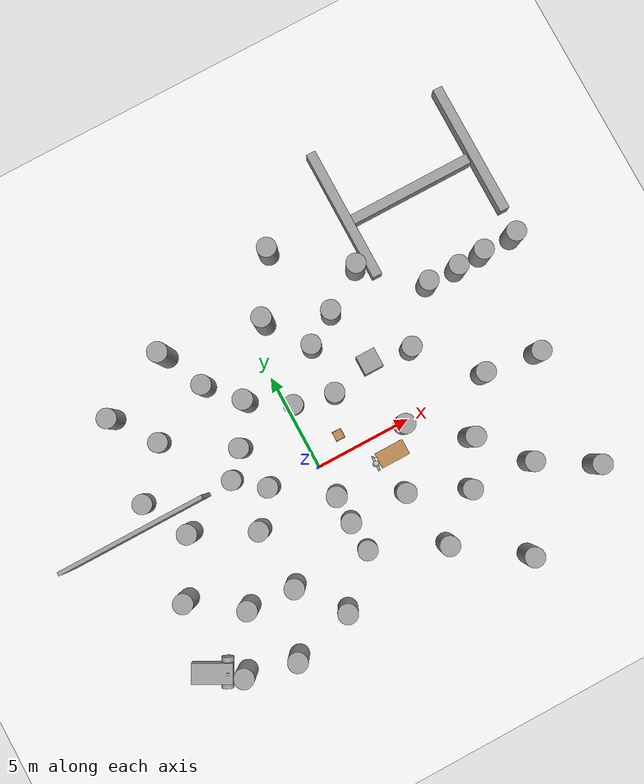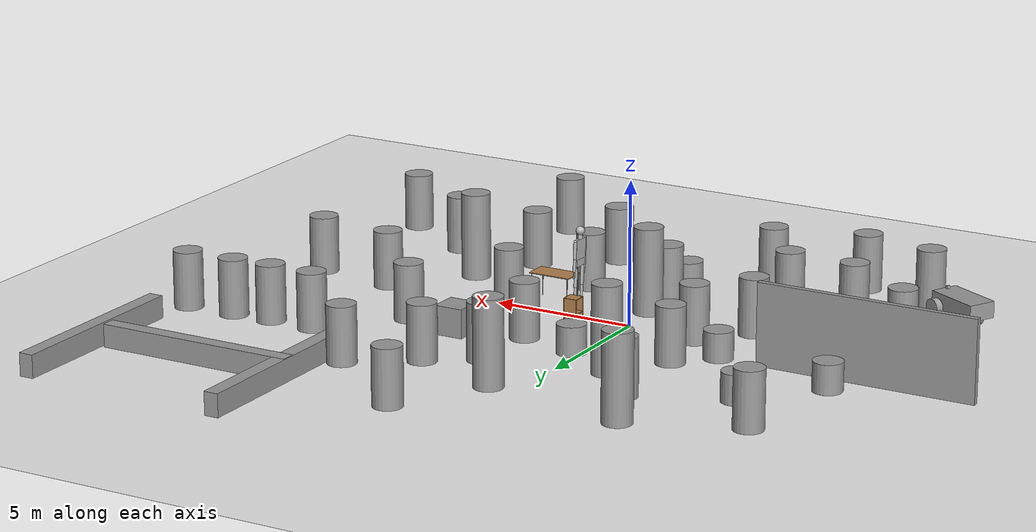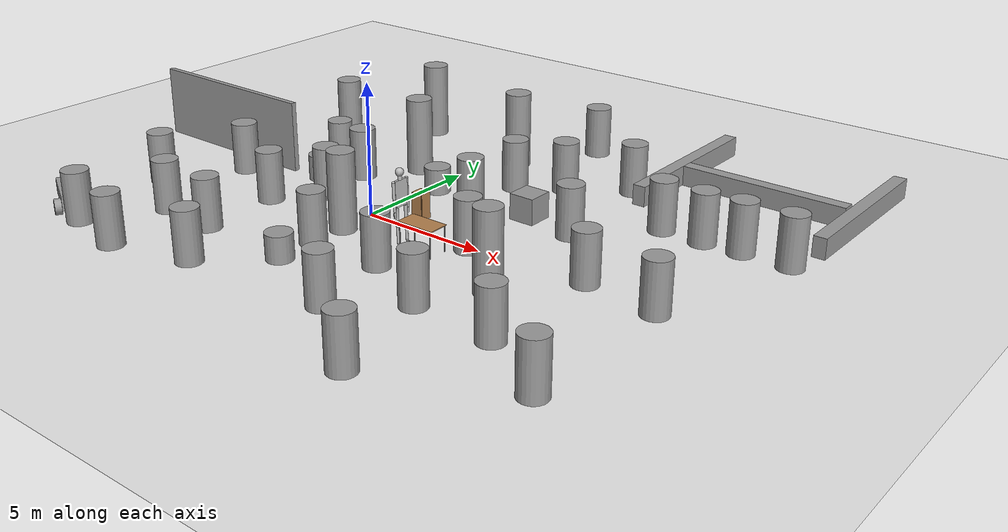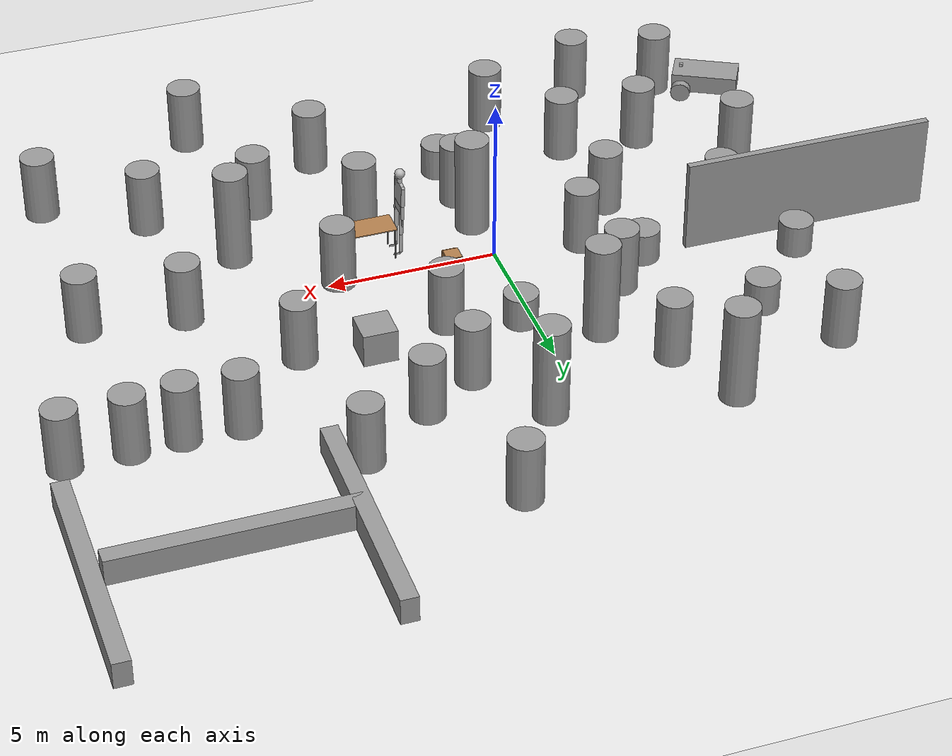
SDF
<sdf version="1.6">
 <world name="default">
  <light name="sun" type="directional">
   <pose>0 0 10 0 -0 0</pose>
   <diffuse>0.8 0.8 0.8 1</diffuse>
   <specular>0.1 0.1 0.1 1</specular>
   <attenuation>
    <range>1000</range>
    <constant>0.9</constant>
    <linear>0.01</linear>
    <quadratic>0.001</quadratic>
   </attenuation>
   <direction>-0.5 0.5 -1</direction>
  </light>
  <model name="ground_plane">
   <static>1</static>
   <link name="link">
    <collision name="collision">
     <geometry><plane><normal>0 0 1</normal><size>100 100</size></plane></geometry>
     <surface><friction><ode><mu>100</mu><mu2>50</mu2></ode></friction></surface>
    </collision>
    <visual name="visual">
     <geometry><plane><normal>0 0 1</normal><size>100 100</size></plane></geometry>
     <material>
      <script><uri>file://media/materials/scripts/gazebo.material</uri><name>Gazebo/White</name></script>
     </material>
    </visual>
   </link>
  </model>
  <physics name="default_physics" default="0" type="ode">
   <ode>
    <solver>
     <type>quick</type>
     <iters>10</iters>
     <sor>1.3</sor>
     <use_dynamic_moi_rescaling>0</use_dynamic_moi_rescaling>
    </solver>
    <constraints>
     <cfm>0</cfm>
     <erp>0.2</erp>
     <contact_max_correcting_vel>100</contact_max_correcting_vel>
     <contact_surface_layer>0.001</contact_surface_layer>
    </constraints>
   </ode>
   <max_step_size>0.004</max_step_size>
   <real_time_factor>1</real_time_factor>
   <real_time_update_rate>250</real_time_update_rate>
  </physics>
  <gravity>0 0 -9.8066</gravity>
  <magnetic_field>6e-06 2.3e-05 -4.2e-05</magnetic_field>
  <atmosphere type="adiabatic"/>
  <scene><ambient>0.4 0.4 0.4 1</ambient><background>0.7 0.7 0.7 1</background><shadows>1</shadows></scene>
  <spherical_coordinates>
   <surface_model>EARTH_WGS84</surface_model>
   <latitude_deg>0</latitude_deg>
   <longitude_deg>0</longitude_deg>
   <elevation>0</elevation>
   <heading_deg>0</heading_deg>
  </spherical_coordinates>
  <model name="unit_cylinder_5">
   <link name="link">
    <inertial>
     <mass>1</mass>
     <inertia><ixx>0.145833</ixx><ixy>0</ixy><ixz>0</ixz><iyy>0.145833</iyy><iyz>0</iyz><izz>0.125</izz></inertia>
    </inertial>
    <visual name="visual">
     <geometry><cylinder><radius>0.5</radius><length>2</length></cylinder></geometry>
     <material>
      <script><name>Gazebo/Grey</name><uri>file://media/materials/scripts/gazebo.material</uri></script>
      <ambient>0.3 0.3 0.3 1</ambient>
      <diffuse>0.7 0.7 0.7 1</diffuse>
      <specular>0.01 0.01 0.01 1</specular>
      <emissive>0 0 0 1</emissive>
      <shader type="vertex"><normal_map>__default__</normal_map></shader>
     </material>
    </visual>
    <collision name="collision">
     <geometry><cylinder><radius>0.5</radius><length>2</length></cylinder></geometry>
     <surface>
      <friction>
       <ode><mu>1</mu><mu2>1</mu2><fdir1>0 0 0</fdir1><slip1>0</slip1><slip2>0</slip2></ode>
       <torsional>
        <coefficient>1</coefficient>
        <patch_radius>0</patch_radius>
        <surface_radius>0</surface_radius>
        <use_patch_radius>1</use_patch_radius>
        <ode><slip>0</slip></ode>
       </torsional>
      </friction>
      <bounce><restitution_coefficient>0</restitution_coefficient><threshold>1e+06</threshold></bounce>
      <contact>
       <collide_without_contact>0</collide_without_contact>
       <collide_without_contact_bitmask>1</collide_without_contact_bitmask>
       <collide_bitmask>1</collide_bitmask>
       <ode>
        <soft_cfm>0</soft_cfm>
        <soft_erp>0.2</soft_erp>
        <kp>1e+13</kp>
        <kd>1</kd>
        <max_vel>0.01</max_vel>
        <min_depth>0</min_depth>
       </ode>
       <bullet>
        <split_impulse>1</split_impulse>
        <split_impulse_penetration_threshold>-0.01</split_impulse_penetration_threshold>
        <soft_cfm>0</soft_cfm>
        <soft_erp>0.2</soft_erp>
        <kp>1e+13</kp>
        <kd>1</kd>
       </bullet>
      </contact>
     </surface>
    </collision>
   </link>
   <static>0</static>
   <pose>4.65515 -0.124311 0.999884 2.2e-05 -2e-06 0.004615</pose>
  </model>
  <model name="unit_cylinder_5">
   <link name="link">
    <inertial>
     <mass>1</mass>
     <inertia><ixx>0.145833</ixx><ixy>0</ixy><ixz>0</ixz><iyy>0.145833</iyy><iyz>0</iyz><izz>0.125</izz></inertia>
    </inertial>
    <visual name="visual">
     <geometry><cylinder><radius>0.5</radius><length>2</length></cylinder></geometry>
     <material>
      <script><name>Gazebo/Grey</name><uri>file://media/materials/scripts/gazebo.material</uri></script>
      <ambient>0.3 0.3 0.3 1</ambient>
      <diffuse>0.7 0.7 0.7 1</diffuse>
      <specular>0.01 0.01 0.01 1</specular>
      <emissive>0 0 0 1</emissive>
      <shader type="vertex"><normal_map>__default__</normal_map></shader>
     </material>
    </visual>
    <collision name="collision">
     <geometry><cylinder><radius>0.5</radius><length>2</length></cylinder></geometry>
     <surface>
      <friction>
       <ode><mu>1</mu><mu2>1</mu2><fdir1>0 0 0</fdir1><slip1>0</slip1><slip2>0</slip2></ode>
       <torsional>
        <coefficient>1</coefficient>
        <patch_radius>0</patch_radius>
        <surface_radius>0</surface_radius>
        <use_patch_radius>1</use_patch_radius>
        <ode><slip>0</slip></ode>
       </torsional>
      </friction>
      <bounce><restitution_coefficient>0</restitution_coefficient><threshold>1e+06</threshold></bounce>
      <contact>
       <collide_without_contact>0</collide_without_contact>
       <collide_without_contact_bitmask>1</collide_without_contact_bitmask>
       <collide_bitmask>1</collide_bitmask>
       <ode>
        <soft_cfm>0</soft_cfm>
        <soft_erp>0.2</soft_erp>
        <kp>1e+13</kp>
        <kd>1</kd>
        <max_vel>0.01</max_vel>
        <min_depth>0</min_depth>
       </ode>
       <bullet>
        <split_impulse>1</split_impulse>
        <split_impulse_penetration_threshold>-0.01</split_impulse_penetration_threshold>
        <soft_cfm>0</soft_cfm>
        <soft_erp>0.2</soft_erp>
        <kp>1e+13</kp>
        <kd>1</kd>
       </bullet>
      </contact>
     </surface>
    </collision>
   </link>
   <static>0</static>
   <pose>4.65515 -0.124311 0.999884 2.2e-05 -2e-06 0.004615</pose>
  </model>
  <model name="unit_cylinder_5_clone">
   <link name="link">
    <inertial>
     <mass>1</mass>
     <inertia><ixx>0.145833</ixx><ixy>0</ixy><ixz>0</ixz><iyy>0.145833</iyy><iyz>0</iyz><izz>0.125</izz></inertia>
    </inertial>
    <visual name="visual">
     <geometry><cylinder><radius>0.5</radius><length>2</length></cylinder></geometry>
     <material>
      <script><name>Gazebo/Grey</name><uri>file://media/materials/scripts/gazebo.material</uri></script>
      <ambient>0.3 0.3 0.3 1</ambient>
      <diffuse>0.7 0.7 0.7 1</diffuse>
      <specular>0.01 0.01 0.01 1</specular>
      <emissive>0 0 0 1</emissive>
      <shader type="vertex"><normal_map>__default__</normal_map></shader>
     </material>
    </visual>
    <collision name="collision">
     <geometry><cylinder><radius>0.5</radius><length>2</length></cylinder></geometry>
     <surface>
      <friction>
       <ode><mu>1</mu><mu2>1</mu2><fdir1>0 0 0</fdir1><slip1>0</slip1><slip2>0</slip2></ode>
       <torsional>
        <coefficient>1</coefficient>
        <patch_radius>0</patch_radius>
        <surface_radius>0</surface_radius>
        <use_patch_radius>1</use_patch_radius>
        <ode><slip>0</slip></ode>
       </torsional>
      </friction>
      <bounce><restitution_coefficient>0</restitution_coefficient><threshold>1e+06</threshold></bounce>
      <contact>
       <collide_without_contact>0</collide_without_contact>
       <collide_without_contact_bitmask>1</collide_without_contact_bitmask>
       <collide_bitmask>1</collide_bitmask>
       <ode>
        <soft_cfm>0</soft_cfm>
        <soft_erp>0.2</soft_erp>
        <kp>1e+13</kp>
        <kd>1</kd>
        <max_vel>0.01</max_vel>
        <min_depth>0</min_depth>
       </ode>
       <bullet>
        <split_impulse>1</split_impulse>
        <split_impulse_penetration_threshold>-0.01</split_impulse_penetration_threshold>
        <soft_cfm>0</soft_cfm>
        <soft_erp>0.2</soft_erp>
        <kp>1e+13</kp>
        <kd>1</kd>
       </bullet>
      </contact>
     </surface>
    </collision>
   </link>
   <static>0</static>
   <pose>2.38828 2.78335 0.999884 2.2e-05 -1e-06 0.002315</pose>
  </model>
  <model name="unit_cylinder_5_clone_0">
   <link name="link">
    <inertial>
     <mass>1</mass>
     <inertia><ixx>0.145833</ixx><ixy>0</ixy><ixz>0</ixz><iyy>0.145833</iyy><iyz>0</iyz><izz>0.125</izz></inertia>
    </inertial>
    <visual name="visual">
     <geometry><cylinder><radius>0.5</radius><length>2</length></cylinder></geometry>
     <material>
      <script><name>Gazebo/Grey</name><uri>file://media/materials/scripts/gazebo.material</uri></script>
      <ambient>0.3 0.3 0.3 1</ambient>
      <diffuse>0.7 0.7 0.7 1</diffuse>
      <specular>0.01 0.01 0.01 1</specular>
      <emissive>0 0 0 1</emissive>
      <shader type="vertex"><normal_map>__default__</normal_map></shader>
     </material>
    </visual>
    <collision name="collision">
     <geometry><cylinder><radius>0.5</radius><length>2</length></cylinder></geometry>
     <surface>
      <friction>
       <ode><mu>1</mu><mu2>1</mu2><fdir1>0 0 0</fdir1><slip1>0</slip1><slip2>0</slip2></ode>
       <torsional>
        <coefficient>1</coefficient>
        <patch_radius>0</patch_radius>
        <surface_radius>0</surface_radius>
        <use_patch_radius>1</use_patch_radius>
        <ode><slip>0</slip></ode>
       </torsional>
      </friction>
      <bounce><restitution_coefficient>0</restitution_coefficient><threshold>1e+06</threshold></bounce>
      <contact>
       <collide_without_contact>0</collide_without_contact>
       <collide_without_contact_bitmask>1</collide_without_contact_bitmask>
       <collide_bitmask>1</collide_bitmask>
       <ode>
        <soft_cfm>0</soft_cfm>
        <soft_erp>0.2</soft_erp>
        <kp>1e+13</kp>
        <kd>1</kd>
        <max_vel>0.01</max_vel>
        <min_depth>0</min_depth>
       </ode>
       <bullet>
        <split_impulse>1</split_impulse>
        <split_impulse_penetration_threshold>-0.01</split_impulse_penetration_threshold>
        <soft_cfm>0</soft_cfm>
        <soft_erp>0.2</soft_erp>
        <kp>1e+13</kp>
        <kd>1</kd>
       </bullet>
      </contact>
     </surface>
    </collision>
   </link>
   <static>0</static>
   <pose>0.149287 -3.03613 0.999884 2.2e-05 -1e-06 0.002298</pose>
  </model>
  <model name="unit_cylinder_5_clone_1">
   <link name="link">
    <inertial>
     <mass>1</mass>
     <inertia><ixx>0.145833</ixx><ixy>0</ixy><ixz>0</ixz><iyy>0.145833</iyy><iyz>0</iyz><izz>0.125</izz></inertia>
    </inertial>
    <visual name="visual">
     <geometry><cylinder><radius>0.5</radius><length>2</length></cylinder></geometry>
     <material>
      <script><name>Gazebo/Grey</name><uri>file://media/materials/scripts/gazebo.material</uri></script>
      <ambient>0.3 0.3 0.3 1</ambient>
      <diffuse>0.7 0.7 0.7 1</diffuse>
      <specular>0.01 0.01 0.01 1</specular>
      <emissive>0 0 0 1</emissive>
      <shader type="vertex"><normal_map>__default__</normal_map></shader>
     </material>
    </visual>
    <collision name="collision">
     <geometry><cylinder><radius>0.5</radius><length>2</length></cylinder></geometry>
     <surface>
      <friction>
       <ode><mu>1</mu><mu2>1</mu2><fdir1>0 0 0</fdir1><slip1>0</slip1><slip2>0</slip2></ode>
       <torsional>
        <coefficient>1</coefficient>
        <patch_radius>0</patch_radius>
        <surface_radius>0</surface_radius>
        <use_patch_radius>1</use_patch_radius>
        <ode><slip>0</slip></ode>
       </torsional>
      </friction>
      <bounce><restitution_coefficient>0</restitution_coefficient><threshold>1e+06</threshold></bounce>
      <contact>
       <collide_without_contact>0</collide_without_contact>
       <collide_without_contact_bitmask>1</collide_without_contact_bitmask>
       <collide_bitmask>1</collide_bitmask>
       <ode>
        <soft_cfm>0</soft_cfm>
        <soft_erp>0.2</soft_erp>
        <kp>1e+13</kp>
        <kd>1</kd>
        <max_vel>0.01</max_vel>
        <min_depth>0</min_depth>
       </ode>
       <bullet>
        <split_impulse>1</split_impulse>
        <split_impulse_penetration_threshold>-0.01</split_impulse_penetration_threshold>
        <soft_cfm>0</soft_cfm>
        <soft_erp>0.2</soft_erp>
        <kp>1e+13</kp>
        <kd>1</kd>
       </bullet>
      </contact>
     </surface>
    </collision>
   </link>
   <static>0</static>
   <pose>-2.86936 2.60725 0.999884 2.2e-05 -1e-06 -0.001918</pose>
  </model>
  <model name="unit_cylinder_5_clone_2">
   <link name="link">
    <inertial>
     <mass>1</mass>
     <inertia><ixx>0.145833</ixx><ixy>0</ixy><ixz>0</ixz><iyy>0.145833</iyy><iyz>0</iyz><izz>0.125</izz></inertia>
    </inertial>
    <visual name="visual">
     <geometry><cylinder><radius>0.5</radius><length>2</length></cylinder></geometry>
     <material>
      <script><name>Gazebo/Grey</name><uri>file://media/materials/scripts/gazebo.material</uri></script>
      <ambient>0.3 0.3 0.3 1</ambient>
      <diffuse>0.7 0.7 0.7 1</diffuse>
      <specular>0.01 0.01 0.01 1</specular>
      <emissive>0 0 0 1</emissive>
      <shader type="vertex"><normal_map>__default__</normal_map></shader>
     </material>
    </visual>
    <collision name="collision">
     <geometry><cylinder><radius>0.5</radius><length>2</length></cylinder></geometry>
     <surface>
      <friction>
       <ode><mu>1</mu><mu2>1</mu2><fdir1>0 0 0</fdir1><slip1>0</slip1><slip2>0</slip2></ode>
       <torsional>
        <coefficient>1</coefficient>
        <patch_radius>0</patch_radius>
        <surface_radius>0</surface_radius>
        <use_patch_radius>1</use_patch_radius>
        <ode><slip>0</slip></ode>
       </torsional>
      </friction>
      <bounce><restitution_coefficient>0</restitution_coefficient><threshold>1e+06</threshold></bounce>
      <contact>
       <collide_without_contact>0</collide_without_contact>
       <collide_without_contact_bitmask>1</collide_without_contact_bitmask>
       <collide_bitmask>1</collide_bitmask>
       <ode>
        <soft_cfm>0</soft_cfm>
        <soft_erp>0.2</soft_erp>
        <kp>1e+13</kp>
        <kd>1</kd>
        <max_vel>0.01</max_vel>
        <min_depth>0</min_depth>
       </ode>
       <bullet>
        <split_impulse>1</split_impulse>
        <split_impulse_penetration_threshold>-0.01</split_impulse_penetration_threshold>
        <soft_cfm>0</soft_cfm>
        <soft_erp>0.2</soft_erp>
        <kp>1e+13</kp>
        <kd>1</kd>
       </bullet>
      </contact>
     </surface>
    </collision>
   </link>
   <static>0</static>
   <pose>-3.88295 -1.30824 0.999884 2.2e-05 -1e-06 0.000184</pose>
  </model>
  <model name="unit_cylinder_5_clone_3">
   <link name="link">
    <inertial>
     <mass>1</mass>
     <inertia><ixx>0.145833</ixx><ixy>0</ixy><ixz>0</ixz><iyy>0.145833</iyy><iyz>0</iyz><izz>0.125</izz></inertia>
    </inertial>
    <visual name="visual">
     <geometry><cylinder><radius>0.5</radius><length>2</length></cylinder></geometry>
     <material>
      <script><name>Gazebo/Grey</name><uri>file://media/materials/scripts/gazebo.material</uri></script>
      <ambient>0.3 0.3 0.3 1</ambient>
      <diffuse>0.7 0.7 0.7 1</diffuse>
      <specular>0.01 0.01 0.01 1</specular>
      <emissive>0 0 0 1</emissive>
      <shader type="vertex"><normal_map>__default__</normal_map></shader>
     </material>
    </visual>
    <collision name="collision">
     <geometry><cylinder><radius>0.5</radius><length>2</length></cylinder></geometry>
     <surface>
      <friction>
       <ode><mu>1</mu><mu2>1</mu2><fdir1>0 0 0</fdir1><slip1>0</slip1><slip2>0</slip2></ode>
       <torsional>
        <coefficient>1</coefficient>
        <patch_radius>0</patch_radius>
        <surface_radius>0</surface_radius>
        <use_patch_radius>1</use_patch_radius>
        <ode><slip>0</slip></ode>
       </torsional>
      </friction>
      <bounce><restitution_coefficient>0</restitution_coefficient><threshold>1e+06</threshold></bounce>
      <contact>
       <collide_without_contact>0</collide_without_contact>
       <collide_without_contact_bitmask>1</collide_without_contact_bitmask>
       <collide_bitmask>1</collide_bitmask>
       <ode>
        <soft_cfm>0</soft_cfm>
        <soft_erp>0.2</soft_erp>
        <kp>1e+13</kp>
        <kd>1</kd>
        <max_vel>0.01</max_vel>
        <min_depth>0</min_depth>
       </ode>
       <bullet>
        <split_impulse>1</split_impulse>
        <split_impulse_penetration_threshold>-0.01</split_impulse_penetration_threshold>
        <soft_cfm>0</soft_cfm>
        <soft_erp>0.2</soft_erp>
        <kp>1e+13</kp>
        <kd>1</kd>
       </bullet>
      </contact>
     </surface>
    </collision>
   </link>
   <static>0</static>
   <pose>-3.66733 -4.47285 0.999884 2.2e-05 -1e-06 0.000409</pose>
  </model>
  <model name="unit_cylinder_5_clone_4">
   <link name="link">
    <inertial>
     <mass>1</mass>
     <inertia><ixx>0.145833</ixx><ixy>0</ixy><ixz>0</ixz><iyy>0.145833</iyy><iyz>0</iyz><izz>0.125</izz></inertia>
    </inertial>
    <visual name="visual">
     <geometry><cylinder><radius>0.5</radius><length>2</length></cylinder></geometry>
     <material>
      <script><name>Gazebo/Grey</name><uri>file://media/materials/scripts/gazebo.material</uri></script>
      <ambient>0.3 0.3 0.3 1</ambient>
      <diffuse>0.7 0.7 0.7 1</diffuse>
      <specular>0.01 0.01 0.01 1</specular>
      <emissive>0 0 0 1</emissive>
      <shader type="vertex"><normal_map>__default__</normal_map></shader>
     </material>
    </visual>
    <collision name="collision">
     <geometry><cylinder><radius>0.5</radius><length>2</length></cylinder></geometry>
     <surface>
      <friction>
       <ode><mu>1</mu><mu2>1</mu2><fdir1>0 0 0</fdir1><slip1>0</slip1><slip2>0</slip2></ode>
       <torsional>
        <coefficient>1</coefficient>
        <patch_radius>0</patch_radius>
        <surface_radius>0</surface_radius>
        <use_patch_radius>1</use_patch_radius>
        <ode><slip>0</slip></ode>
       </torsional>
      </friction>
      <bounce><restitution_coefficient>0</restitution_coefficient><threshold>1e+06</threshold></bounce>
      <contact>
       <collide_without_contact>0</collide_without_contact>
       <collide_without_contact_bitmask>1</collide_without_contact_bitmask>
       <collide_bitmask>1</collide_bitmask>
       <ode>
        <soft_cfm>0</soft_cfm>
        <soft_erp>0.2</soft_erp>
        <kp>1e+13</kp>
        <kd>1</kd>
        <max_vel>0.01</max_vel>
        <min_depth>0</min_depth>
       </ode>
       <bullet>
        <split_impulse>1</split_impulse>
        <split_impulse_penetration_threshold>-0.01</split_impulse_penetration_threshold>
        <soft_cfm>0</soft_cfm>
        <soft_erp>0.2</soft_erp>
        <kp>1e+13</kp>
        <kd>1</kd>
       </bullet>
      </contact>
     </surface>
    </collision>
   </link>
   <static>0</static>
   <pose>-6.93374 0.169664 0.999884 2.2e-05 -1e-06 -0.003062</pose>
  </model>
  <model name="unit_cylinder_5_clone_5">
   <link name="link">
    <inertial>
     <mass>1</mass>
     <inertia><ixx>0.145833</ixx><ixy>0</ixy><ixz>0</ixz><iyy>0.145833</iyy><iyz>0</iyz><izz>0.125</izz></inertia>
    </inertial>
    <visual name="visual">
     <geometry><cylinder><radius>0.5</radius><length>2</length></cylinder></geometry>
     <material>
      <script><name>Gazebo/Grey</name><uri>file://media/materials/scripts/gazebo.material</uri></script>
      <ambient>0.3 0.3 0.3 1</ambient>
      <diffuse>0.7 0.7 0.7 1</diffuse>
      <specular>0.01 0.01 0.01 1</specular>
      <emissive>0 0 0 1</emissive>
      <shader type="vertex"><normal_map>__default__</normal_map></shader>
     </material>
    </visual>
    <collision name="collision">
     <geometry><cylinder><radius>0.5</radius><length>2</length></cylinder></geometry>
     <surface>
      <friction>
       <ode><mu>1</mu><mu2>1</mu2><fdir1>0 0 0</fdir1><slip1>0</slip1><slip2>0</slip2></ode>
       <torsional>
        <coefficient>1</coefficient>
        <patch_radius>0</patch_radius>
        <surface_radius>0</surface_radius>
        <use_patch_radius>1</use_patch_radius>
        <ode><slip>0</slip></ode>
       </torsional>
      </friction>
      <bounce><restitution_coefficient>0</restitution_coefficient><threshold>1e+06</threshold></bounce>
      <contact>
       <collide_without_contact>0</collide_without_contact>
       <collide_without_contact_bitmask>1</collide_without_contact_bitmask>
       <collide_bitmask>1</collide_bitmask>
       <ode>
        <soft_cfm>0</soft_cfm>
        <soft_erp>0.2</soft_erp>
        <kp>1e+13</kp>
        <kd>1</kd>
        <max_vel>0.01</max_vel>
        <min_depth>0</min_depth>
       </ode>
       <bullet>
        <split_impulse>1</split_impulse>
        <split_impulse_penetration_threshold>-0.01</split_impulse_penetration_threshold>
        <soft_cfm>0</soft_cfm>
        <soft_erp>0.2</soft_erp>
        <kp>1e+13</kp>
        <kd>1</kd>
       </bullet>
      </contact>
     </surface>
    </collision>
   </link>
   <static>0</static>
   <pose>-8.58869 -2.60629 0.999884 2.2e-05 -1e-06 -0.00547</pose>
  </model>
  <model name="unit_cylinder_5_clone_6">
   <link name="link">
    <inertial>
     <mass>1</mass>
     <inertia><ixx>0.145833</ixx><ixy>0</ixy><ixz>0</ixz><iyy>0.145833</iyy><iyz>0</iyz><izz>0.125</izz></inertia>
    </inertial>
    <visual name="visual">
     <geometry><cylinder><radius>0.5</radius><length>2</length></cylinder></geometry>
     <material>
      <script><name>Gazebo/Grey</name><uri>file://media/materials/scripts/gazebo.material</uri></script>
      <ambient>0.3 0.3 0.3 1</ambient>
      <diffuse>0.7 0.7 0.7 1</diffuse>
      <specular>0.01 0.01 0.01 1</specular>
      <emissive>0 0 0 1</emissive>
      <shader type="vertex"><normal_map>__default__</normal_map></shader>
     </material>
    </visual>
    <collision name="collision">
     <geometry><cylinder><radius>0.5</radius><length>2</length></cylinder></geometry>
     <surface>
      <friction>
       <ode><mu>1</mu><mu2>1</mu2><fdir1>0 0 0</fdir1><slip1>0</slip1><slip2>0</slip2></ode>
       <torsional>
        <coefficient>1</coefficient>
        <patch_radius>0</patch_radius>
        <surface_radius>0</surface_radius>
        <use_patch_radius>1</use_patch_radius>
        <ode><slip>0</slip></ode>
       </torsional>
      </friction>
      <bounce><restitution_coefficient>0</restitution_coefficient><threshold>1e+06</threshold></bounce>
      <contact>
       <collide_without_contact>0</collide_without_contact>
       <collide_without_contact_bitmask>1</collide_without_contact_bitmask>
       <collide_bitmask>1</collide_bitmask>
       <ode>
        <soft_cfm>0</soft_cfm>
        <soft_erp>0.2</soft_erp>
        <kp>1e+13</kp>
        <kd>1</kd>
        <max_vel>0.01</max_vel>
        <min_depth>0</min_depth>
       </ode>
       <bullet>
        <split_impulse>1</split_impulse>
        <split_impulse_penetration_threshold>-0.01</split_impulse_penetration_threshold>
        <soft_cfm>0</soft_cfm>
        <soft_erp>0.2</soft_erp>
        <kp>1e+13</kp>
        <kd>1</kd>
       </bullet>
      </contact>
     </surface>
    </collision>
   </link>
   <static>0</static>
   <pose>6.68619 2.97584 0.999884 2.2e-05 -1e-06 1.9e-05</pose>
  </model>
  <model name="unit_cylinder_5_clone_7">
   <link name="link">
    <inertial>
     <mass>1</mass>
     <inertia><ixx>0.145833</ixx><ixy>0</ixy><ixz>0</ixz><iyy>0.145833</iyy><iyz>0</iyz><izz>0.125</izz></inertia>
    </inertial>
    <visual name="visual">
     <geometry><cylinder><radius>0.5</radius><length>2</length></cylinder></geometry>
     <material>
      <script><name>Gazebo/Grey</name><uri>file://media/materials/scripts/gazebo.material</uri></script>
      <ambient>0.3 0.3 0.3 1</ambient>
      <diffuse>0.7 0.7 0.7 1</diffuse>
      <specular>0.01 0.01 0.01 1</specular>
      <emissive>0 0 0 1</emissive>
      <shader type="vertex"><normal_map>__default__</normal_map></shader>
     </material>
    </visual>
    <collision name="collision">
     <geometry><cylinder><radius>0.5</radius><length>2</length></cylinder></geometry>
     <surface>
      <friction>
       <ode><mu>1</mu><mu2>1</mu2><fdir1>0 0 0</fdir1><slip1>0</slip1><slip2>0</slip2></ode>
       <torsional>
        <coefficient>1</coefficient>
        <patch_radius>0</patch_radius>
        <surface_radius>0</surface_radius>
        <use_patch_radius>1</use_patch_radius>
        <ode><slip>0</slip></ode>
       </torsional>
      </friction>
      <bounce><restitution_coefficient>0</restitution_coefficient><threshold>1e+06</threshold></bounce>
      <contact>
       <collide_without_contact>0</collide_without_contact>
       <collide_without_contact_bitmask>1</collide_without_contact_bitmask>
       <collide_bitmask>1</collide_bitmask>
       <ode>
        <soft_cfm>0</soft_cfm>
        <soft_erp>0.2</soft_erp>
        <kp>1e+13</kp>
        <kd>1</kd>
        <max_vel>0.01</max_vel>
        <min_depth>0</min_depth>
       </ode>
       <bullet>
        <split_impulse>1</split_impulse>
        <split_impulse_penetration_threshold>-0.01</split_impulse_penetration_threshold>
        <soft_cfm>0</soft_cfm>
        <soft_erp>0.2</soft_erp>
        <kp>1e+13</kp>
        <kd>1</kd>
       </bullet>
      </contact>
     </surface>
    </collision>
   </link>
   <static>0</static>
   <pose>5.97232 -4.3731 0.999884 2.2e-05 -1e-06 0.002884</pose>
  </model>
  <model name="unit_cylinder_0">
   <pose>0.360811 3.27692 0.499884 3e-06 -3e-06 -0.000418</pose>
   <link name="link">
    <inertial>
     <mass>1</mass>
     <inertia><ixx>0.145833</ixx><ixy>0</ixy><ixz>0</ixz><iyy>0.145833</iyy><iyz>0</iyz><izz>0.125</izz></inertia>
    </inertial>
    <collision name="collision">
     <geometry><cylinder><radius>0.5</radius><length>1</length></cylinder></geometry>
    </collision>
    <visual name="visual">
     <geometry><cylinder><radius>0.5</radius><length>1</length></cylinder></geometry>
     <material>
      <script><name>Gazebo/Grey</name><uri>file://media/materials/scripts/gazebo.material</uri></script>
     </material>
    </visual>
   </link>
  </model>
  <model name="unit_box_0">
   <pose>4.62964 3.37332 0.499944 2e-06 0.000108 -0.001429</pose>
   <link name="link">
    <inertial>
     <mass>1</mass>
     <inertia>
      <ixx>0.166667</ixx>
      <ixy>0</ixy>
      <ixz>0</ixz>
      <iyy>0.166667</iyy>
      <iyz>0</iyz>
      <izz>0.166667</izz>
     </inertia>
    </inertial>
    <collision name="collision"><geometry><box><size>1 1 1</size></box></geometry></collision>
    <visual name="visual">
     <geometry><box><size>1 1 1</size></box></geometry>
     <material>
      <script><name>Gazebo/Grey</name><uri>file://media/materials/scripts/gazebo.material</uri></script>
     </material>
    </visual>
   </link>
  </model>
  <model name="unit_cylinder_1">
   <pose>0.210065 -4.63987 0.499884 3e-06 -3e-06 -0.000165</pose>
   <link name="link">
    <inertial>
     <mass>1</mass>
     <inertia><ixx>0.145833</ixx><ixy>0</ixy><ixz>0</ixz><iyy>0.145833</iyy><iyz>0</iyz><izz>0.125</izz></inertia>
    </inertial>
    <collision name="collision">
     <geometry><cylinder><radius>0.5</radius><length>1</length></cylinder></geometry>
    </collision>
    <visual name="visual">
     <geometry><cylinder><radius>0.5</radius><length>1</length></cylinder></geometry>
     <material>
      <script><name>Gazebo/Grey</name><uri>file://media/materials/scripts/gazebo.material</uri></script>
     </material>
    </visual>
   </link>
  </model>
  <model name="unit_cylinder_1_clone">
   <pose>-4.00192 1.44993 0.499972 -5.4e-05 5.5e-05 -0.000151</pose>
   <link name="link">
    <inertial>
     <mass>1</mass>
     <inertia><ixx>0.145833</ixx><ixy>0</ixy><ixz>0</ixz><iyy>0.145833</iyy><iyz>0</iyz><izz>0.125</izz></inertia>
    </inertial>
    <collision name="collision">
     <geometry><cylinder><radius>0.5</radius><length>1</length></cylinder></geometry>
    </collision>
    <visual name="visual">
     <geometry><cylinder><radius>0.5</radius><length>1</length></cylinder></geometry>
     <material>
      <script><name>Gazebo/Grey</name><uri>file://media/materials/scripts/gazebo.material</uri></script>
     </material>
    </visual>
   </link>
  </model>
  <model name="unit_cylinder_1_clone_0">
   <pose>-6.29638 4.76436 0.499972 -5.4e-05 5.5e-05 -0.000122</pose>
   <link name="link">
    <inertial>
     <mass>1</mass>
     <inertia><ixx>0.145833</ixx><ixy>0</ixy><ixz>0</ixz><iyy>0.145833</iyy><iyz>0</iyz><izz>0.125</izz></inertia>
    </inertial>
    <collision name="collision">
     <geometry><cylinder><radius>0.5</radius><length>1</length></cylinder></geometry>
    </collision>
    <visual name="visual">
     <geometry><cylinder><radius>0.5</radius><length>1</length></cylinder></geometry>
     <material>
      <script><name>Gazebo/Grey</name><uri>file://media/materials/scripts/gazebo.material</uri></script>
     </material>
    </visual>
   </link>
  </model>
  <model name="unit_cylinder_1_clone_1">
   <pose>-8.33577 2.47754 0.499972 -5.4e-05 5.5e-05 0.001407</pose>
   <link name="link">
    <inertial>
     <mass>1</mass>
     <inertia><ixx>0.145833</ixx><ixy>0</ixy><ixz>0</ixz><iyy>0.145833</iyy><iyz>0</iyz><izz>0.125</izz></inertia>
    </inertial>
    <collision name="collision">
     <geometry><cylinder><radius>0.5</radius><length>1</length></cylinder></geometry>
    </collision>
    <visual name="visual">
     <geometry><cylinder><radius>0.5</radius><length>1</length></cylinder></geometry>
     <material>
      <script><name>Gazebo/Grey</name><uri>file://media/materials/scripts/gazebo.material</uri></script>
     </material>
    </visual>
   </link>
  </model>
  <model name="unit_cylinder_0_0">
   <link name="link">
    <inertial>
     <mass>1</mass>
     <inertia><ixx>0.145833</ixx><ixy>0</ixy><ixz>0</ixz><iyy>0.145833</iyy><iyz>0</iyz><izz>0.125</izz></inertia>
    </inertial>
    <visual name="visual">
     <geometry><cylinder><radius>0.5</radius><length>3</length></cylinder></geometry>
     <material>
      <script><name>Gazebo/Grey</name><uri>file://media/materials/scripts/gazebo.material</uri></script>
      <ambient>0.3 0.3 0.3 1</ambient>
      <diffuse>0.7 0.7 0.7 1</diffuse>
      <specular>0.01 0.01 0.01 1</specular>
      <emissive>0 0 0 1</emissive>
      <shader type="vertex"><normal_map>__default__</normal_map></shader>
     </material>
    </visual>
    <collision name="collision">
     <geometry><cylinder><radius>0.5</radius><length>3</length></cylinder></geometry>
     <surface>
      <friction>
       <ode><mu>1</mu><mu2>1</mu2><fdir1>0 0 0</fdir1><slip1>0</slip1><slip2>0</slip2></ode>
       <torsional>
        <coefficient>1</coefficient>
        <patch_radius>0</patch_radius>
        <surface_radius>0</surface_radius>
        <use_patch_radius>1</use_patch_radius>
        <ode><slip>0</slip></ode>
       </torsional>
      </friction>
      <bounce><restitution_coefficient>0</restitution_coefficient><threshold>1e+06</threshold></bounce>
      <contact>
       <collide_without_contact>0</collide_without_contact>
       <collide_without_contact_bitmask>1</collide_without_contact_bitmask>
       <collide_bitmask>1</collide_bitmask>
       <ode>
        <soft_cfm>0</soft_cfm>
        <soft_erp>0.2</soft_erp>
        <kp>1e+13</kp>
        <kd>1</kd>
        <max_vel>0.01</max_vel>
        <min_depth>0</min_depth>
       </ode>
       <bullet>
        <split_impulse>1</split_impulse>
        <split_impulse_penetration_threshold>-0.01</split_impulse_penetration_threshold>
        <soft_cfm>0</soft_cfm>
        <soft_erp>0.2</soft_erp>
        <kp>1e+13</kp>
        <kd>1</kd>
       </bullet>
      </contact>
     </surface>
    </collision>
   </link>
   <static>0</static>
   <pose>7.16627 -2.19502 1.49988 4.7e-05 -4e-06 -0.002805</pose>
  </model>
  <model name="unit_cylinder_0_0_clone">
   <link name="link">
    <inertial>
     <mass>1</mass>
     <inertia><ixx>0.145833</ixx><ixy>0</ixy><ixz>0</ixz><iyy>0.145833</iyy><iyz>0</iyz><izz>0.125</izz></inertia>
    </inertial>
    <visual name="visual">
     <geometry><cylinder><radius>0.5</radius><length>3</length></cylinder></geometry>
     <material>
      <script><name>Gazebo/Grey</name><uri>file://media/materials/scripts/gazebo.material</uri></script>
      <ambient>0.3 0.3 0.3 1</ambient>
      <diffuse>0.7 0.7 0.7 1</diffuse>
      <specular>0.01 0.01 0.01 1</specular>
      <emissive>0 0 0 1</emissive>
      <shader type="vertex"><normal_map>__default__</normal_map></shader>
     </material>
    </visual>
    <collision name="collision">
     <geometry><cylinder><radius>0.5</radius><length>3</length></cylinder></geometry>
     <surface>
      <friction>
       <ode><mu>1</mu><mu2>1</mu2><fdir1>0 0 0</fdir1><slip1>0</slip1><slip2>0</slip2></ode>
       <torsional>
        <coefficient>1</coefficient>
        <patch_radius>0</patch_radius>
        <surface_radius>0</surface_radius>
        <use_patch_radius>1</use_patch_radius>
        <ode><slip>0</slip></ode>
       </torsional>
      </friction>
      <bounce><restitution_coefficient>0</restitution_coefficient><threshold>1e+06</threshold></bounce>
      <contact>
       <collide_without_contact>0</collide_without_contact>
       <collide_without_contact_bitmask>1</collide_without_contact_bitmask>
       <collide_bitmask>1</collide_bitmask>
       <ode>
        <soft_cfm>0</soft_cfm>
        <soft_erp>0.2</soft_erp>
        <kp>1e+13</kp>
        <kd>1</kd>
        <max_vel>0.01</max_vel>
        <min_depth>0</min_depth>
       </ode>
       <bullet>
        <split_impulse>1</split_impulse>
        <split_impulse_penetration_threshold>-0.01</split_impulse_penetration_threshold>
        <soft_cfm>0</soft_cfm>
        <soft_erp>0.2</soft_erp>
        <kp>1e+13</kp>
        <kd>1</kd>
       </bullet>
      </contact>
     </surface>
    </collision>
   </link>
   <static>0</static>
   <pose>0.153962 -1.584 1.49988 4.7e-05 4e-06 0.006839</pose>
  </model>
  <model name="unit_cylinder_5_clone_1_clone">
   <link name="link">
    <inertial>
     <mass>1</mass>
     <inertia><ixx>0.145833</ixx><ixy>0</ixy><ixz>0</ixz><iyy>0.145833</iyy><iyz>0</iyz><izz>0.125</izz></inertia>
    </inertial>
    <visual name="visual">
     <geometry><cylinder><radius>0.5</radius><length>2</length></cylinder></geometry>
     <material>
      <script><name>Gazebo/Grey</name><uri>file://media/materials/scripts/gazebo.material</uri></script>
      <ambient>0.3 0.3 0.3 1</ambient>
      <diffuse>0.7 0.7 0.7 1</diffuse>
      <specular>0.01 0.01 0.01 1</specular>
      <emissive>0 0 0 1</emissive>
      <shader type="vertex"><normal_map>__default__</normal_map></shader>
     </material>
    </visual>
    <collision name="collision">
     <geometry><cylinder><radius>0.5</radius><length>2</length></cylinder></geometry>
     <surface>
      <friction>
       <ode><mu>1</mu><mu2>1</mu2><fdir1>0 0 0</fdir1><slip1>0</slip1><slip2>0</slip2></ode>
       <torsional>
        <coefficient>1</coefficient>
        <patch_radius>0</patch_radius>
        <surface_radius>0</surface_radius>
        <use_patch_radius>1</use_patch_radius>
        <ode><slip>0</slip></ode>
       </torsional>
      </friction>
      <bounce><restitution_coefficient>0</restitution_coefficient><threshold>1e+06</threshold></bounce>
      <contact>
       <collide_without_contact>0</collide_without_contact>
       <collide_without_contact_bitmask>1</collide_without_contact_bitmask>
       <collide_bitmask>1</collide_bitmask>
       <ode>
        <soft_cfm>0</soft_cfm>
        <soft_erp>0.2</soft_erp>
        <kp>1e+13</kp>
        <kd>1</kd>
        <max_vel>0.01</max_vel>
        <min_depth>0</min_depth>
       </ode>
       <bullet>
        <split_impulse>1</split_impulse>
        <split_impulse_penetration_threshold>-0.01</split_impulse_penetration_threshold>
        <soft_cfm>0</soft_cfm>
        <soft_erp>0.2</soft_erp>
        <kp>1e+13</kp>
        <kd>1</kd>
       </bullet>
      </contact>
     </surface>
    </collision>
   </link>
   <static>0</static>
   <pose>2.48657 5.3464 0.999884 2.2e-05 -1e-06 -0.002392</pose>
  </model>
  <model name="unit_cylinder_5_clone_1_clone_0">
   <link name="link">
    <inertial>
     <mass>1</mass>
     <inertia><ixx>0.145833</ixx><ixy>0</ixy><ixz>0</ixz><iyy>0.145833</iyy><iyz>0</iyz><izz>0.125</izz></inertia>
    </inertial>
    <visual name="visual">
     <geometry><cylinder><radius>0.5</radius><length>2</length></cylinder></geometry>
     <material>
      <script><name>Gazebo/Grey</name><uri>file://media/materials/scripts/gazebo.material</uri></script>
      <ambient>0.3 0.3 0.3 1</ambient>
      <diffuse>0.7 0.7 0.7 1</diffuse>
      <specular>0.01 0.01 0.01 1</specular>
      <emissive>0 0 0 1</emissive>
      <shader type="vertex"><normal_map>__default__</normal_map></shader>
     </material>
    </visual>
    <collision name="collision">
     <geometry><cylinder><radius>0.5</radius><length>2</length></cylinder></geometry>
     <surface>
      <friction>
       <ode><mu>1</mu><mu2>1</mu2><fdir1>0 0 0</fdir1><slip1>0</slip1><slip2>0</slip2></ode>
       <torsional>
        <coefficient>1</coefficient>
        <patch_radius>0</patch_radius>
        <surface_radius>0</surface_radius>
        <use_patch_radius>1</use_patch_radius>
        <ode><slip>0</slip></ode>
       </torsional>
      </friction>
      <bounce><restitution_coefficient>0</restitution_coefficient><threshold>1e+06</threshold></bounce>
      <contact>
       <collide_without_contact>0</collide_without_contact>
       <collide_without_contact_bitmask>1</collide_without_contact_bitmask>
       <collide_bitmask>1</collide_bitmask>
       <ode>
        <soft_cfm>0</soft_cfm>
        <soft_erp>0.2</soft_erp>
        <kp>1e+13</kp>
        <kd>1</kd>
        <max_vel>0.01</max_vel>
        <min_depth>0</min_depth>
       </ode>
       <bullet>
        <split_impulse>1</split_impulse>
        <split_impulse_penetration_threshold>-0.01</split_impulse_penetration_threshold>
        <soft_cfm>0</soft_cfm>
        <soft_erp>0.2</soft_erp>
        <kp>1e+13</kp>
        <kd>1</kd>
       </bullet>
      </contact>
     </surface>
    </collision>
   </link>
   <static>0</static>
   <pose>-3.04049 6.13018 0.999884 2.2e-05 -1e-06 -0.001363</pose>
  </model>
  <model name="unit_cylinder_0_0_clone_clone">
   <link name="link">
    <inertial>
     <mass>1</mass>
     <inertia><ixx>0.145833</ixx><ixy>0</ixy><ixz>0</ixz><iyy>0.145833</iyy><iyz>0</iyz><izz>0.125</izz></inertia>
    </inertial>
    <visual name="visual">
     <geometry><cylinder><radius>0.5</radius><length>3</length></cylinder></geometry>
     <material>
      <script><name>Gazebo/Grey</name><uri>file://media/materials/scripts/gazebo.material</uri></script>
      <ambient>0.3 0.3 0.3 1</ambient>
      <diffuse>0.7 0.7 0.7 1</diffuse>
      <specular>0.01 0.01 0.01 1</specular>
      <emissive>0 0 0 1</emissive>
      <shader type="vertex"><normal_map>__default__</normal_map></shader>
     </material>
    </visual>
    <collision name="collision">
     <geometry><cylinder><radius>0.5</radius><length>3</length></cylinder></geometry>
     <surface>
      <friction>
       <ode><mu>1</mu><mu2>1</mu2><fdir1>0 0 0</fdir1><slip1>0</slip1><slip2>0</slip2></ode>
       <torsional>
        <coefficient>1</coefficient>
        <patch_radius>0</patch_radius>
        <surface_radius>0</surface_radius>
        <use_patch_radius>1</use_patch_radius>
        <ode><slip>0</slip></ode>
       </torsional>
      </friction>
      <bounce><restitution_coefficient>0</restitution_coefficient><threshold>1e+06</threshold></bounce>
      <contact>
       <collide_without_contact>0</collide_without_contact>
       <collide_without_contact_bitmask>1</collide_without_contact_bitmask>
       <collide_bitmask>1</collide_bitmask>
       <ode>
        <soft_cfm>0</soft_cfm>
        <soft_erp>0.2</soft_erp>
        <kp>1e+13</kp>
        <kd>1</kd>
        <max_vel>0.01</max_vel>
        <min_depth>0</min_depth>
       </ode>
       <bullet>
        <split_impulse>1</split_impulse>
        <split_impulse_penetration_threshold>-0.01</split_impulse_penetration_threshold>
        <soft_cfm>0</soft_cfm>
        <soft_erp>0.2</soft_erp>
        <kp>1e+13</kp>
        <kd>1</kd>
       </bullet>
      </contact>
     </surface>
    </collision>
   </link>
   <static>0</static>
   <pose>1.00231 7.45946 1.49988 4.7e-05 -4e-06 -0.006467</pose>
  </model>
  <model name="unit_cylinder_0_0_clone_clone_0">
   <link name="link">
    <inertial>
     <mass>1</mass>
     <inertia><ixx>0.145833</ixx><ixy>0</ixy><ixz>0</ixz><iyy>0.145833</iyy><iyz>0</iyz><izz>0.125</izz></inertia>
    </inertial>
    <visual name="visual">
     <geometry><cylinder><radius>0.5</radius><length>3</length></cylinder></geometry>
     <material>
      <script><name>Gazebo/Grey</name><uri>file://media/materials/scripts/gazebo.material</uri></script>
      <ambient>0.3 0.3 0.3 1</ambient>
      <diffuse>0.7 0.7 0.7 1</diffuse>
      <specular>0.01 0.01 0.01 1</specular>
      <emissive>0 0 0 1</emissive>
      <shader type="vertex"><normal_map>__default__</normal_map></shader>
     </material>
    </visual>
    <collision name="collision">
     <geometry><cylinder><radius>0.5</radius><length>3</length></cylinder></geometry>
     <surface>
      <friction>
       <ode><mu>1</mu><mu2>1</mu2><fdir1>0 0 0</fdir1><slip1>0</slip1><slip2>0</slip2></ode>
       <torsional>
        <coefficient>1</coefficient>
        <patch_radius>0</patch_radius>
        <surface_radius>0</surface_radius>
        <use_patch_radius>1</use_patch_radius>
        <ode><slip>0</slip></ode>
       </torsional>
      </friction>
      <bounce><restitution_coefficient>0</restitution_coefficient><threshold>1e+06</threshold></bounce>
      <contact>
       <collide_without_contact>0</collide_without_contact>
       <collide_without_contact_bitmask>1</collide_without_contact_bitmask>
       <collide_bitmask>1</collide_bitmask>
       <ode>
        <soft_cfm>0</soft_cfm>
        <soft_erp>0.2</soft_erp>
        <kp>1e+13</kp>
        <kd>1</kd>
        <max_vel>0.01</max_vel>
        <min_depth>0</min_depth>
       </ode>
       <bullet>
        <split_impulse>1</split_impulse>
        <split_impulse_penetration_threshold>-0.01</split_impulse_penetration_threshold>
        <soft_cfm>0</soft_cfm>
        <soft_erp>0.2</soft_erp>
        <kp>1e+13</kp>
        <kd>1</kd>
       </bullet>
      </contact>
     </surface>
    </collision>
   </link>
   <static>0</static>
   <pose>-4.03855 8.32066 1.49988 4.7e-05 -4e-06 -0.002883</pose>
  </model>
  <model name="unit_cylinder_0_0_clone_clone_1">
   <link name="link">
    <inertial>
     <mass>1</mass>
     <inertia><ixx>0.145833</ixx><ixy>0</ixy><ixz>0</ixz><iyy>0.145833</iyy><iyz>0</iyz><izz>0.125</izz></inertia>
    </inertial>
    <visual name="visual">
     <geometry><cylinder><radius>0.5</radius><length>3</length></cylinder></geometry>
     <material>
      <script><name>Gazebo/Grey</name><uri>file://media/materials/scripts/gazebo.material</uri></script>
      <ambient>0.3 0.3 0.3 1</ambient>
      <diffuse>0.7 0.7 0.7 1</diffuse>
      <specular>0.01 0.01 0.01 1</specular>
      <emissive>0 0 0 1</emissive>
      <shader type="vertex"><normal_map>__default__</normal_map></shader>
     </material>
    </visual>
    <collision name="collision">
     <geometry><cylinder><radius>0.5</radius><length>3</length></cylinder></geometry>
     <surface>
      <friction>
       <ode><mu>1</mu><mu2>1</mu2><fdir1>0 0 0</fdir1><slip1>0</slip1><slip2>0</slip2></ode>
       <torsional>
        <coefficient>1</coefficient>
        <patch_radius>0</patch_radius>
        <surface_radius>0</surface_radius>
        <use_patch_radius>1</use_patch_radius>
        <ode><slip>0</slip></ode>
       </torsional>
      </friction>
      <bounce><restitution_coefficient>0</restitution_coefficient><threshold>1e+06</threshold></bounce>
      <contact>
       <collide_without_contact>0</collide_without_contact>
       <collide_without_contact_bitmask>1</collide_without_contact_bitmask>
       <collide_bitmask>1</collide_bitmask>
       <ode>
        <soft_cfm>0</soft_cfm>
        <soft_erp>0.2</soft_erp>
        <kp>1e+13</kp>
        <kd>1</kd>
        <max_vel>0.01</max_vel>
        <min_depth>0</min_depth>
       </ode>
       <bullet>
        <split_impulse>1</split_impulse>
        <split_impulse_penetration_threshold>-0.01</split_impulse_penetration_threshold>
        <soft_cfm>0</soft_cfm>
        <soft_erp>0.2</soft_erp>
        <kp>1e+13</kp>
        <kd>1</kd>
       </bullet>
      </contact>
     </surface>
    </collision>
   </link>
   <static>0</static>
   <pose>-1.56798 4.46718 1.49988 4.7e-05 4e-06 0.003118</pose>
  </model>
  <model name="unit_cylinder_5_clone_0_clone">
   <link name="link">
    <inertial>
     <mass>1</mass>
     <inertia><ixx>0.145833</ixx><ixy>0</ixy><ixz>0</ixz><iyy>0.145833</iyy><iyz>0</iyz><izz>0.125</izz></inertia>
    </inertial>
    <visual name="visual">
     <geometry><cylinder><radius>0.5</radius><length>2</length></cylinder></geometry>
     <material>
      <script><name>Gazebo/Grey</name><uri>file://media/materials/scripts/gazebo.material</uri></script>
      <ambient>0.3 0.3 0.3 1</ambient>
      <diffuse>0.7 0.7 0.7 1</diffuse>
      <specular>0.01 0.01 0.01 1</specular>
      <emissive>0 0 0 1</emissive>
      <shader type="vertex"><normal_map>__default__</normal_map></shader>
     </material>
    </visual>
    <collision name="collision">
     <geometry><cylinder><radius>0.5</radius><length>2</length></cylinder></geometry>
     <surface>
      <friction>
       <ode><mu>1</mu><mu2>1</mu2><fdir1>0 0 0</fdir1><slip1>0</slip1><slip2>0</slip2></ode>
       <torsional>
        <coefficient>1</coefficient>
        <patch_radius>0</patch_radius>
        <surface_radius>0</surface_radius>
        <use_patch_radius>1</use_patch_radius>
        <ode><slip>0</slip></ode>
       </torsional>
      </friction>
      <bounce><restitution_coefficient>0</restitution_coefficient><threshold>1e+06</threshold></bounce>
      <contact>
       <collide_without_contact>0</collide_without_contact>
       <collide_without_contact_bitmask>1</collide_without_contact_bitmask>
       <collide_bitmask>1</collide_bitmask>
       <ode>
        <soft_cfm>0</soft_cfm>
        <soft_erp>0.2</soft_erp>
        <kp>1e+13</kp>
        <kd>1</kd>
        <max_vel>0.01</max_vel>
        <min_depth>0</min_depth>
       </ode>
       <bullet>
        <split_impulse>1</split_impulse>
        <split_impulse_penetration_threshold>-0.01</split_impulse_penetration_threshold>
        <soft_cfm>0</soft_cfm>
        <soft_erp>0.2</soft_erp>
        <kp>1e+13</kp>
        <kd>1</kd>
       </bullet>
      </contact>
     </surface>
    </collision>
   </link>
   <static>0</static>
   <pose>3.1338 -3.03548 0.999884 2.2e-05 -2e-06 0.003543</pose>
  </model>
  <model name="unit_cylinder_5_clone_0_clone_0">
   <link name="link">
    <inertial>
     <mass>1</mass>
     <inertia><ixx>0.145833</ixx><ixy>0</ixy><ixz>0</ixz><iyy>0.145833</iyy><iyz>0</iyz><izz>0.125</izz></inertia>
    </inertial>
    <visual name="visual">
     <geometry><cylinder><radius>0.5</radius><length>2</length></cylinder></geometry>
     <material>
      <script><name>Gazebo/Grey</name><uri>file://media/materials/scripts/gazebo.material</uri></script>
      <ambient>0.3 0.3 0.3 1</ambient>
      <diffuse>0.7 0.7 0.7 1</diffuse>
      <specular>0.01 0.01 0.01 1</specular>
      <emissive>0 0 0 1</emissive>
      <shader type="vertex"><normal_map>__default__</normal_map></shader>
     </material>
    </visual>
    <collision name="collision">
     <geometry><cylinder><radius>0.5</radius><length>2</length></cylinder></geometry>
     <surface>
      <friction>
       <ode><mu>1</mu><mu2>1</mu2><fdir1>0 0 0</fdir1><slip1>0</slip1><slip2>0</slip2></ode>
       <torsional>
        <coefficient>1</coefficient>
        <patch_radius>0</patch_radius>
        <surface_radius>0</surface_radius>
        <use_patch_radius>1</use_patch_radius>
        <ode><slip>0</slip></ode>
       </torsional>
      </friction>
      <bounce><restitution_coefficient>0</restitution_coefficient><threshold>1e+06</threshold></bounce>
      <contact>
       <collide_without_contact>0</collide_without_contact>
       <collide_without_contact_bitmask>1</collide_without_contact_bitmask>
       <collide_bitmask>1</collide_bitmask>
       <ode>
        <soft_cfm>0</soft_cfm>
        <soft_erp>0.2</soft_erp>
        <kp>1e+13</kp>
        <kd>1</kd>
        <max_vel>0.01</max_vel>
        <min_depth>0</min_depth>
       </ode>
       <bullet>
        <split_impulse>1</split_impulse>
        <split_impulse_penetration_threshold>-0.01</split_impulse_penetration_threshold>
        <soft_cfm>0</soft_cfm>
        <soft_erp>0.2</soft_erp>
        <kp>1e+13</kp>
        <kd>1</kd>
       </bullet>
      </contact>
     </surface>
    </collision>
   </link>
   <static>0</static>
   <pose>-2.53712 0.299352 0.999884 2.2e-05 -1e-06 0.002126</pose>
  </model>
  <model name="unit_cylinder_5_clone_0_clone_1">
   <link name="link">
    <inertial>
     <mass>1</mass>
     <inertia><ixx>0.145833</ixx><ixy>0</ixy><ixz>0</ixz><iyy>0.145833</iyy><iyz>0</iyz><izz>0.125</izz></inertia>
    </inertial>
    <visual name="visual">
     <geometry><cylinder><radius>0.5</radius><length>2</length></cylinder></geometry>
     <material>
      <script><name>Gazebo/Grey</name><uri>file://media/materials/scripts/gazebo.material</uri></script>
      <ambient>0.3 0.3 0.3 1</ambient>
      <diffuse>0.7 0.7 0.7 1</diffuse>
      <specular>0.01 0.01 0.01 1</specular>
      <emissive>0 0 0 1</emissive>
      <shader type="vertex"><normal_map>__default__</normal_map></shader>
     </material>
    </visual>
    <collision name="collision">
     <geometry><cylinder><radius>0.5</radius><length>2</length></cylinder></geometry>
     <surface>
      <friction>
       <ode><mu>1</mu><mu2>1</mu2><fdir1>0 0 0</fdir1><slip1>0</slip1><slip2>0</slip2></ode>
       <torsional>
        <coefficient>1</coefficient>
        <patch_radius>0</patch_radius>
        <surface_radius>0</surface_radius>
        <use_patch_radius>1</use_patch_radius>
        <ode><slip>0</slip></ode>
       </torsional>
      </friction>
      <bounce><restitution_coefficient>0</restitution_coefficient><threshold>1e+06</threshold></bounce>
      <contact>
       <collide_without_contact>0</collide_without_contact>
       <collide_without_contact_bitmask>1</collide_without_contact_bitmask>
       <collide_bitmask>1</collide_bitmask>
       <ode>
        <soft_cfm>0</soft_cfm>
        <soft_erp>0.2</soft_erp>
        <kp>1e+13</kp>
        <kd>1</kd>
        <max_vel>0.01</max_vel>
        <min_depth>0</min_depth>
       </ode>
       <bullet>
        <split_impulse>1</split_impulse>
        <split_impulse_penetration_threshold>-0.01</split_impulse_penetration_threshold>
        <soft_cfm>0</soft_cfm>
        <soft_erp>0.2</soft_erp>
        <kp>1e+13</kp>
        <kd>1</kd>
       </bullet>
      </contact>
     </surface>
    </collision>
   </link>
   <static>0</static>
   <pose>-1.98793 -6.68673 0.999884 2.2e-05 -1e-06 0.00217</pose>
  </model>
  <model name="unit_cylinder_5_clone_0_clone_2">
   <link name="link">
    <inertial>
     <mass>1</mass>
     <inertia><ixx>0.145833</ixx><ixy>0</ixy><ixz>0</ixz><iyy>0.145833</iyy><iyz>0</iyz><izz>0.125</izz></inertia>
    </inertial>
    <visual name="visual">
     <geometry><cylinder><radius>0.5</radius><length>2</length></cylinder></geometry>
     <material>
      <script><name>Gazebo/Grey</name><uri>file://media/materials/scripts/gazebo.material</uri></script>
      <ambient>0.3 0.3 0.3 1</ambient>
      <diffuse>0.7 0.7 0.7 1</diffuse>
      <specular>0.01 0.01 0.01 1</specular>
      <emissive>0 0 0 1</emissive>
      <shader type="vertex"><normal_map>__default__</normal_map></shader>
     </material>
    </visual>
    <collision name="collision">
     <geometry><cylinder><radius>0.5</radius><length>2</length></cylinder></geometry>
     <surface>
      <friction>
       <ode><mu>1</mu><mu2>1</mu2><fdir1>0 0 0</fdir1><slip1>0</slip1><slip2>0</slip2></ode>
       <torsional>
        <coefficient>1</coefficient>
        <patch_radius>0</patch_radius>
        <surface_radius>0</surface_radius>
        <use_patch_radius>1</use_patch_radius>
        <ode><slip>0</slip></ode>
       </torsional>
      </friction>
      <bounce><restitution_coefficient>0</restitution_coefficient><threshold>1e+06</threshold></bounce>
      <contact>
       <collide_without_contact>0</collide_without_contact>
       <collide_without_contact_bitmask>1</collide_without_contact_bitmask>
       <collide_bitmask>1</collide_bitmask>
       <ode>
        <soft_cfm>0</soft_cfm>
        <soft_erp>0.2</soft_erp>
        <kp>1e+13</kp>
        <kd>1</kd>
        <max_vel>0.01</max_vel>
        <min_depth>0</min_depth>
       </ode>
       <bullet>
        <split_impulse>1</split_impulse>
        <split_impulse_penetration_threshold>-0.01</split_impulse_penetration_threshold>
        <soft_cfm>0</soft_cfm>
        <soft_erp>0.2</soft_erp>
        <kp>1e+13</kp>
        <kd>1</kd>
       </bullet>
      </contact>
     </surface>
    </collision>
   </link>
   <static>0</static>
   <pose>3.74075 -6.1902 0.999884 2.2e-05 -1e-06 0.002509</pose>
  </model>
  <model name="unit_cylinder_5_clone_0_clone_4">
   <link name="link">
    <inertial>
     <mass>1</mass>
     <inertia><ixx>0.145833</ixx><ixy>0</ixy><ixz>0</ixz><iyy>0.145833</iyy><iyz>0</iyz><izz>0.125</izz></inertia>
    </inertial>
    <visual name="visual">
     <geometry><cylinder><radius>0.5</radius><length>2</length></cylinder></geometry>
     <material>
      <script><name>Gazebo/Grey</name><uri>file://media/materials/scripts/gazebo.material</uri></script>
      <ambient>0.3 0.3 0.3 1</ambient>
      <diffuse>0.7 0.7 0.7 1</diffuse>
      <specular>0.01 0.01 0.01 1</specular>
      <emissive>0 0 0 1</emissive>
      <shader type="vertex"><normal_map>__default__</normal_map></shader>
     </material>
    </visual>
    <collision name="collision">
     <geometry><cylinder><radius>0.5</radius><length>2</length></cylinder></geometry>
     <surface>
      <friction>
       <ode><mu>1</mu><mu2>1</mu2><fdir1>0 0 0</fdir1><slip1>0</slip1><slip2>0</slip2></ode>
       <torsional>
        <coefficient>1</coefficient>
        <patch_radius>0</patch_radius>
        <surface_radius>0</surface_radius>
        <use_patch_radius>1</use_patch_radius>
        <ode><slip>0</slip></ode>
       </torsional>
      </friction>
      <bounce><restitution_coefficient>0</restitution_coefficient><threshold>1e+06</threshold></bounce>
      <contact>
       <collide_without_contact>0</collide_without_contact>
       <collide_without_contact_bitmask>1</collide_without_contact_bitmask>
       <collide_bitmask>1</collide_bitmask>
       <ode>
        <soft_cfm>0</soft_cfm>
        <soft_erp>0.2</soft_erp>
        <kp>1e+13</kp>
        <kd>1</kd>
        <max_vel>0.01</max_vel>
        <min_depth>0</min_depth>
       </ode>
       <bullet>
        <split_impulse>1</split_impulse>
        <split_impulse_penetration_threshold>-0.01</split_impulse_penetration_threshold>
        <soft_cfm>0</soft_cfm>
        <soft_erp>0.2</soft_erp>
        <kp>1e+13</kp>
        <kd>1</kd>
       </bullet>
      </contact>
     </surface>
    </collision>
   </link>
   <static>0</static>
   <pose>6.23609 7.78207 0.999884 2.2e-05 -1e-06 0.001775</pose>
  </model>
  <model name="unit_cylinder_5_clone_0_clone_5">
   <link name="link">
    <inertial>
     <mass>1</mass>
     <inertia><ixx>0.145833</ixx><ixy>0</ixy><ixz>0</ixz><iyy>0.145833</iyy><iyz>0</iyz><izz>0.125</izz></inertia>
    </inertial>
    <visual name="visual">
     <geometry><cylinder><radius>0.5</radius><length>2</length></cylinder></geometry>
     <material>
      <script><name>Gazebo/Grey</name><uri>file://media/materials/scripts/gazebo.material</uri></script>
      <ambient>0.3 0.3 0.3 1</ambient>
      <diffuse>0.7 0.7 0.7 1</diffuse>
      <specular>0.01 0.01 0.01 1</specular>
      <emissive>0 0 0 1</emissive>
      <shader type="vertex"><normal_map>__default__</normal_map></shader>
     </material>
    </visual>
    <collision name="collision">
     <geometry><cylinder><radius>0.5</radius><length>2</length></cylinder></geometry>
     <surface>
      <friction>
       <ode><mu>1</mu><mu2>1</mu2><fdir1>0 0 0</fdir1><slip1>0</slip1><slip2>0</slip2></ode>
       <torsional>
        <coefficient>1</coefficient>
        <patch_radius>0</patch_radius>
        <surface_radius>0</surface_radius>
        <use_patch_radius>1</use_patch_radius>
        <ode><slip>0</slip></ode>
       </torsional>
      </friction>
      <bounce><restitution_coefficient>0</restitution_coefficient><threshold>1e+06</threshold></bounce>
      <contact>
       <collide_without_contact>0</collide_without_contact>
       <collide_without_contact_bitmask>1</collide_without_contact_bitmask>
       <collide_bitmask>1</collide_bitmask>
       <ode>
        <soft_cfm>0</soft_cfm>
        <soft_erp>0.2</soft_erp>
        <kp>1e+13</kp>
        <kd>1</kd>
        <max_vel>0.01</max_vel>
        <min_depth>0</min_depth>
       </ode>
       <bullet>
        <split_impulse>1</split_impulse>
        <split_impulse_penetration_threshold>-0.01</split_impulse_penetration_threshold>
        <soft_cfm>0</soft_cfm>
        <soft_erp>0.2</soft_erp>
        <kp>1e+13</kp>
        <kd>1</kd>
       </bullet>
      </contact>
     </surface>
    </collision>
   </link>
   <static>0</static>
   <pose>4.1001 6.37052 0.999884 2.2e-05 -1e-06 0.001515</pose>
  </model>
  <model name="unit_cylinder_5_clone_0_clone_6">
   <link name="link">
    <inertial>
     <mass>1</mass>
     <inertia><ixx>0.145833</ixx><ixy>0</ixy><ixz>0</ixz><iyy>0.145833</iyy><iyz>0</iyz><izz>0.125</izz></inertia>
    </inertial>
    <visual name="visual">
     <geometry><cylinder><radius>0.5</radius><length>2</length></cylinder></geometry>
     <material>
      <script><name>Gazebo/Grey</name><uri>file://media/materials/scripts/gazebo.material</uri></script>
      <ambient>0.3 0.3 0.3 1</ambient>
      <diffuse>0.7 0.7 0.7 1</diffuse>
      <specular>0.01 0.01 0.01 1</specular>
      <emissive>0 0 0 1</emissive>
      <shader type="vertex"><normal_map>__default__</normal_map></shader>
     </material>
    </visual>
    <collision name="collision">
     <geometry><cylinder><radius>0.5</radius><length>2</length></cylinder></geometry>
     <surface>
      <friction>
       <ode><mu>1</mu><mu2>1</mu2><fdir1>0 0 0</fdir1><slip1>0</slip1><slip2>0</slip2></ode>
       <torsional>
        <coefficient>1</coefficient>
        <patch_radius>0</patch_radius>
        <surface_radius>0</surface_radius>
        <use_patch_radius>1</use_patch_radius>
        <ode><slip>0</slip></ode>
       </torsional>
      </friction>
      <bounce><restitution_coefficient>0</restitution_coefficient><threshold>1e+06</threshold></bounce>
      <contact>
       <collide_without_contact>0</collide_without_contact>
       <collide_without_contact_bitmask>1</collide_without_contact_bitmask>
       <collide_bitmask>1</collide_bitmask>
       <ode>
        <soft_cfm>0</soft_cfm>
        <soft_erp>0.2</soft_erp>
        <kp>1e+13</kp>
        <kd>1</kd>
        <max_vel>0.01</max_vel>
        <min_depth>0</min_depth>
       </ode>
       <bullet>
        <split_impulse>1</split_impulse>
        <split_impulse_penetration_threshold>-0.01</split_impulse_penetration_threshold>
        <soft_cfm>0</soft_cfm>
        <soft_erp>0.2</soft_erp>
        <kp>1e+13</kp>
        <kd>1</kd>
       </bullet>
      </contact>
     </surface>
    </collision>
   </link>
   <static>0</static>
   <pose>-7.74649 6.83601 0.999884 2.2e-05 -1e-06 0.001447</pose>
  </model>
  <model name="unit_cylinder_5_clone_0_clone_7">
   <link name="link">
    <inertial>
     <mass>1</mass>
     <inertia><ixx>0.145833</ixx><ixy>0</ixy><ixz>0</ixz><iyy>0.145833</iyy><iyz>0</iyz><izz>0.125</izz></inertia>
    </inertial>
    <visual name="visual">
     <geometry><cylinder><radius>0.5</radius><length>2</length></cylinder></geometry>
     <material>
      <script><name>Gazebo/Grey</name><uri>file://media/materials/scripts/gazebo.material</uri></script>
      <ambient>0.3 0.3 0.3 1</ambient>
      <diffuse>0.7 0.7 0.7 1</diffuse>
      <specular>0.01 0.01 0.01 1</specular>
      <emissive>0 0 0 1</emissive>
      <shader type="vertex"><normal_map>__default__</normal_map></shader>
     </material>
    </visual>
    <collision name="collision">
     <geometry><cylinder><radius>0.5</radius><length>2</length></cylinder></geometry>
     <surface>
      <friction>
       <ode><mu>1</mu><mu2>1</mu2><fdir1>0 0 0</fdir1><slip1>0</slip1><slip2>0</slip2></ode>
       <torsional>
        <coefficient>1</coefficient>
        <patch_radius>0</patch_radius>
        <surface_radius>0</surface_radius>
        <use_patch_radius>1</use_patch_radius>
        <ode><slip>0</slip></ode>
       </torsional>
      </friction>
      <bounce><restitution_coefficient>0</restitution_coefficient><threshold>1e+06</threshold></bounce>
      <contact>
       <collide_without_contact>0</collide_without_contact>
       <collide_without_contact_bitmask>1</collide_without_contact_bitmask>
       <collide_bitmask>1</collide_bitmask>
       <ode>
        <soft_cfm>0</soft_cfm>
        <soft_erp>0.2</soft_erp>
        <kp>1e+13</kp>
        <kd>1</kd>
        <max_vel>0.01</max_vel>
        <min_depth>0</min_depth>
       </ode>
       <bullet>
        <split_impulse>1</split_impulse>
        <split_impulse_penetration_threshold>-0.01</split_impulse_penetration_threshold>
        <soft_cfm>0</soft_cfm>
        <soft_erp>0.2</soft_erp>
        <kp>1e+13</kp>
        <kd>1</kd>
       </bullet>
      </contact>
     </surface>
    </collision>
   </link>
   <static>0</static>
   <pose>-6.09067 -4.32212 0.999884 2.2e-05 -1e-06 0.000922</pose>
  </model>
  <model name="unit_cylinder_5_clone_0_clone_8">
   <link name="link">
    <inertial>
     <mass>1</mass>
     <inertia><ixx>0.145833</ixx><ixy>0</ixy><ixz>0</ixz><iyy>0.145833</iyy><iyz>0</iyz><izz>0.125</izz></inertia>
    </inertial>
    <visual name="visual">
     <geometry><cylinder><radius>0.5</radius><length>2</length></cylinder></geometry>
     <material>
      <script><name>Gazebo/Grey</name><uri>file://media/materials/scripts/gazebo.material</uri></script>
      <ambient>0.3 0.3 0.3 1</ambient>
      <diffuse>0.7 0.7 0.7 1</diffuse>
      <specular>0.01 0.01 0.01 1</specular>
      <emissive>0 0 0 1</emissive>
      <shader type="vertex"><normal_map>__default__</normal_map></shader>
     </material>
    </visual>
    <collision name="collision">
     <geometry><cylinder><radius>0.5</radius><length>2</length></cylinder></geometry>
     <surface>
      <friction>
       <ode><mu>1</mu><mu2>1</mu2><fdir1>0 0 0</fdir1><slip1>0</slip1><slip2>0</slip2></ode>
       <torsional>
        <coefficient>1</coefficient>
        <patch_radius>0</patch_radius>
        <surface_radius>0</surface_radius>
        <use_patch_radius>1</use_patch_radius>
        <ode><slip>0</slip></ode>
       </torsional>
      </friction>
      <bounce><restitution_coefficient>0</restitution_coefficient><threshold>1e+06</threshold></bounce>
      <contact>
       <collide_without_contact>0</collide_without_contact>
       <collide_without_contact_bitmask>1</collide_without_contact_bitmask>
       <collide_bitmask>1</collide_bitmask>
       <ode>
        <soft_cfm>0</soft_cfm>
        <soft_erp>0.2</soft_erp>
        <kp>1e+13</kp>
        <kd>1</kd>
        <max_vel>0.01</max_vel>
        <min_depth>0</min_depth>
       </ode>
       <bullet>
        <split_impulse>1</split_impulse>
        <split_impulse_penetration_threshold>-0.01</split_impulse_penetration_threshold>
        <soft_cfm>0</soft_cfm>
        <soft_erp>0.2</soft_erp>
        <kp>1e+13</kp>
        <kd>1</kd>
       </bullet>
      </contact>
     </surface>
    </collision>
   </link>
   <static>0</static>
   <pose>-7.67513 -7.00939 0.999884 2.2e-05 -1e-06 0.000229</pose>
  </model>
  <model name="unit_cylinder_5_clone_0_clone_9">
   <link name="link">
    <inertial>
     <mass>1</mass>
     <inertia><ixx>0.145833</ixx><ixy>0</ixy><ixz>0</ixz><iyy>0.145833</iyy><iyz>0</iyz><izz>0.125</izz></inertia>
    </inertial>
    <visual name="visual">
     <geometry><cylinder><radius>0.5</radius><length>2</length></cylinder></geometry>
     <material>
      <script><name>Gazebo/Grey</name><uri>file://media/materials/scripts/gazebo.material</uri></script>
      <ambient>0.3 0.3 0.3 1</ambient>
      <diffuse>0.7 0.7 0.7 1</diffuse>
      <specular>0.01 0.01 0.01 1</specular>
      <emissive>0 0 0 1</emissive>
      <shader type="vertex"><normal_map>__default__</normal_map></shader>
     </material>
    </visual>
    <collision name="collision">
     <geometry><cylinder><radius>0.5</radius><length>2</length></cylinder></geometry>
     <surface>
      <friction>
       <ode><mu>1</mu><mu2>1</mu2><fdir1>0 0 0</fdir1><slip1>0</slip1><slip2>0</slip2></ode>
       <torsional>
        <coefficient>1</coefficient>
        <patch_radius>0</patch_radius>
        <surface_radius>0</surface_radius>
        <use_patch_radius>1</use_patch_radius>
        <ode><slip>0</slip></ode>
       </torsional>
      </friction>
      <bounce><restitution_coefficient>0</restitution_coefficient><threshold>1e+06</threshold></bounce>
      <contact>
       <collide_without_contact>0</collide_without_contact>
       <collide_without_contact_bitmask>1</collide_without_contact_bitmask>
       <collide_bitmask>1</collide_bitmask>
       <ode>
        <soft_cfm>0</soft_cfm>
        <soft_erp>0.2</soft_erp>
        <kp>1e+13</kp>
        <kd>1</kd>
        <max_vel>0.01</max_vel>
        <min_depth>0</min_depth>
       </ode>
       <bullet>
        <split_impulse>1</split_impulse>
        <split_impulse_penetration_threshold>-0.01</split_impulse_penetration_threshold>
        <soft_cfm>0</soft_cfm>
        <soft_erp>0.2</soft_erp>
        <kp>1e+13</kp>
        <kd>1</kd>
       </bullet>
      </contact>
     </surface>
    </collision>
   </link>
   <static>0</static>
   <pose>-5.11629 -7.54674 0.999884 2.2e-05 -1e-06 0.000681</pose>
  </model>
  <model name="unit_cylinder_5_clone_7_clone">
   <link name="link">
    <inertial>
     <mass>1</mass>
     <inertia><ixx>0.145833</ixx><ixy>0</ixy><ixz>0</ixz><iyy>0.145833</iyy><iyz>0</iyz><izz>0.125</izz></inertia>
    </inertial>
    <visual name="visual">
     <geometry><cylinder><radius>0.5</radius><length>2</length></cylinder></geometry>
     <material>
      <script><name>Gazebo/Grey</name><uri>file://media/materials/scripts/gazebo.material</uri></script>
      <ambient>0.3 0.3 0.3 1</ambient>
      <diffuse>0.7 0.7 0.7 1</diffuse>
      <specular>0.01 0.01 0.01 1</specular>
      <emissive>0 0 0 1</emissive>
      <shader type="vertex"><normal_map>__default__</normal_map></shader>
     </material>
    </visual>
    <collision name="collision">
     <geometry><cylinder><radius>0.5</radius><length>2</length></cylinder></geometry>
     <surface>
      <friction>
       <ode><mu>1</mu><mu2>1</mu2><fdir1>0 0 0</fdir1><slip1>0</slip1><slip2>0</slip2></ode>
       <torsional>
        <coefficient>1</coefficient>
        <patch_radius>0</patch_radius>
        <surface_radius>0</surface_radius>
        <use_patch_radius>1</use_patch_radius>
        <ode><slip>0</slip></ode>
       </torsional>
      </friction>
      <bounce><restitution_coefficient>0</restitution_coefficient><threshold>1e+06</threshold></bounce>
      <contact>
       <collide_without_contact>0</collide_without_contact>
       <collide_without_contact_bitmask>1</collide_without_contact_bitmask>
       <collide_bitmask>1</collide_bitmask>
       <ode>
        <soft_cfm>0</soft_cfm>
        <soft_erp>0.2</soft_erp>
        <kp>1e+13</kp>
        <kd>1</kd>
        <max_vel>0.01</max_vel>
        <min_depth>0</min_depth>
       </ode>
       <bullet>
        <split_impulse>1</split_impulse>
        <split_impulse_penetration_threshold>-0.01</split_impulse_penetration_threshold>
        <soft_cfm>0</soft_cfm>
        <soft_erp>0.2</soft_erp>
        <kp>1e+13</kp>
        <kd>1</kd>
       </bullet>
      </contact>
     </surface>
    </collision>
   </link>
   <static>0</static>
   <pose>8.9336 5.3909 0.999884 2.2e-05 -1e-06 0.002182</pose>
  </model>
  <model name="unit_cylinder_5_clone_7_clone_0">
   <link name="link">
    <inertial>
     <mass>1</mass>
     <inertia><ixx>0.145833</ixx><ixy>0</ixy><ixz>0</ixz><iyy>0.145833</iyy><iyz>0</iyz><izz>0.125</izz></inertia>
    </inertial>
    <visual name="visual">
     <geometry><cylinder><radius>0.5</radius><length>2</length></cylinder></geometry>
     <material>
      <script><name>Gazebo/Grey</name><uri>file://media/materials/scripts/gazebo.material</uri></script>
      <ambient>0.3 0.3 0.3 1</ambient>
      <diffuse>0.7 0.7 0.7 1</diffuse>
      <specular>0.01 0.01 0.01 1</specular>
      <emissive>0 0 0 1</emissive>
      <shader type="vertex"><normal_map>__default__</normal_map></shader>
     </material>
    </visual>
    <collision name="collision">
     <geometry><cylinder><radius>0.5</radius><length>2</length></cylinder></geometry>
     <surface>
      <friction>
       <ode><mu>1</mu><mu2>1</mu2><fdir1>0 0 0</fdir1><slip1>0</slip1><slip2>0</slip2></ode>
       <torsional>
        <coefficient>1</coefficient>
        <patch_radius>0</patch_radius>
        <surface_radius>0</surface_radius>
        <use_patch_radius>1</use_patch_radius>
        <ode><slip>0</slip></ode>
       </torsional>
      </friction>
      <bounce><restitution_coefficient>0</restitution_coefficient><threshold>1e+06</threshold></bounce>
      <contact>
       <collide_without_contact>0</collide_without_contact>
       <collide_without_contact_bitmask>1</collide_without_contact_bitmask>
       <collide_bitmask>1</collide_bitmask>
       <ode>
        <soft_cfm>0</soft_cfm>
        <soft_erp>0.2</soft_erp>
        <kp>1e+13</kp>
        <kd>1</kd>
        <max_vel>0.01</max_vel>
        <min_depth>0</min_depth>
       </ode>
       <bullet>
        <split_impulse>1</split_impulse>
        <split_impulse_penetration_threshold>-0.01</split_impulse_penetration_threshold>
        <soft_cfm>0</soft_cfm>
        <soft_erp>0.2</soft_erp>
        <kp>1e+13</kp>
        <kd>1</kd>
       </bullet>
      </contact>
     </surface>
    </collision>
   </link>
   <static>0</static>
   <pose>10.566 5.36923 0.999884 2.2e-05 -1e-06 0.002145</pose>
  </model>
  <model name="unit_cylinder_5_clone_7_clone_1">
   <link name="link">
    <inertial>
     <mass>1</mass>
     <inertia><ixx>0.145833</ixx><ixy>0</ixy><ixz>0</ixz><iyy>0.145833</iyy><iyz>0</iyz><izz>0.125</izz></inertia>
    </inertial>
    <visual name="visual">
     <geometry><cylinder><radius>0.5</radius><length>2</length></cylinder></geometry>
     <material>
      <script><name>Gazebo/Grey</name><uri>file://media/materials/scripts/gazebo.material</uri></script>
      <ambient>0.3 0.3 0.3 1</ambient>
      <diffuse>0.7 0.7 0.7 1</diffuse>
      <specular>0.01 0.01 0.01 1</specular>
      <emissive>0 0 0 1</emissive>
      <shader type="vertex"><normal_map>__default__</normal_map></shader>
     </material>
    </visual>
    <collision name="collision">
     <geometry><cylinder><radius>0.5</radius><length>2</length></cylinder></geometry>
     <surface>
      <friction>
       <ode><mu>1</mu><mu2>1</mu2><fdir1>0 0 0</fdir1><slip1>0</slip1><slip2>0</slip2></ode>
       <torsional>
        <coefficient>1</coefficient>
        <patch_radius>0</patch_radius>
        <surface_radius>0</surface_radius>
        <use_patch_radius>1</use_patch_radius>
        <ode><slip>0</slip></ode>
       </torsional>
      </friction>
      <bounce><restitution_coefficient>0</restitution_coefficient><threshold>1e+06</threshold></bounce>
      <contact>
       <collide_without_contact>0</collide_without_contact>
       <collide_without_contact_bitmask>1</collide_without_contact_bitmask>
       <collide_bitmask>1</collide_bitmask>
       <ode>
        <soft_cfm>0</soft_cfm>
        <soft_erp>0.2</soft_erp>
        <kp>1e+13</kp>
        <kd>1</kd>
        <max_vel>0.01</max_vel>
        <min_depth>0</min_depth>
       </ode>
       <bullet>
        <split_impulse>1</split_impulse>
        <split_impulse_penetration_threshold>-0.01</split_impulse_penetration_threshold>
        <soft_cfm>0</soft_cfm>
        <soft_erp>0.2</soft_erp>
        <kp>1e+13</kp>
        <kd>1</kd>
       </bullet>
      </contact>
     </surface>
    </collision>
   </link>
   <static>0</static>
   <pose>11.9935 5.45437 0.999884 2.2e-05 -1e-06 0.002185</pose>
  </model>
  <model name="unit_cylinder_5_clone_7_clone_2">
   <link name="link">
    <inertial>
     <mass>1</mass>
     <inertia><ixx>0.145833</ixx><ixy>0</ixy><ixz>0</ixz><iyy>0.145833</iyy><iyz>0</iyz><izz>0.125</izz></inertia>
    </inertial>
    <visual name="visual">
     <geometry><cylinder><radius>0.5</radius><length>2</length></cylinder></geometry>
     <material>
      <script><name>Gazebo/Grey</name><uri>file://media/materials/scripts/gazebo.material</uri></script>
      <ambient>0.3 0.3 0.3 1</ambient>
      <diffuse>0.7 0.7 0.7 1</diffuse>
      <specular>0.01 0.01 0.01 1</specular>
      <emissive>0 0 0 1</emissive>
      <shader type="vertex"><normal_map>__default__</normal_map></shader>
     </material>
    </visual>
    <collision name="collision">
     <geometry><cylinder><radius>0.5</radius><length>2</length></cylinder></geometry>
     <surface>
      <friction>
       <ode><mu>1</mu><mu2>1</mu2><fdir1>0 0 0</fdir1><slip1>0</slip1><slip2>0</slip2></ode>
       <torsional>
        <coefficient>1</coefficient>
        <patch_radius>0</patch_radius>
        <surface_radius>0</surface_radius>
        <use_patch_radius>1</use_patch_radius>
        <ode><slip>0</slip></ode>
       </torsional>
      </friction>
      <bounce><restitution_coefficient>0</restitution_coefficient><threshold>1e+06</threshold></bounce>
      <contact>
       <collide_without_contact>0</collide_without_contact>
       <collide_without_contact_bitmask>1</collide_without_contact_bitmask>
       <collide_bitmask>1</collide_bitmask>
       <ode>
        <soft_cfm>0</soft_cfm>
        <soft_erp>0.2</soft_erp>
        <kp>1e+13</kp>
        <kd>1</kd>
        <max_vel>0.01</max_vel>
        <min_depth>0</min_depth>
       </ode>
       <bullet>
        <split_impulse>1</split_impulse>
        <split_impulse_penetration_threshold>-0.01</split_impulse_penetration_threshold>
        <soft_cfm>0</soft_cfm>
        <soft_erp>0.2</soft_erp>
        <kp>1e+13</kp>
        <kd>1</kd>
       </bullet>
      </contact>
     </surface>
    </collision>
   </link>
   <static>0</static>
   <pose>13.789 5.49374 0.999884 2.2e-05 -1e-06 0.002209</pose>
  </model>
  <model name="unit_cylinder_5_clone_7_clone_4">
   <link name="link">
    <inertial>
     <mass>1</mass>
     <inertia><ixx>0.145833</ixx><ixy>0</ixy><ixz>0</ixz><iyy>0.145833</iyy><iyz>0</iyz><izz>0.125</izz></inertia>
    </inertial>
    <visual name="visual">
     <geometry><cylinder><radius>0.5</radius><length>2</length></cylinder></geometry>
     <material>
      <script><name>Gazebo/Grey</name><uri>file://media/materials/scripts/gazebo.material</uri></script>
      <ambient>0.3 0.3 0.3 1</ambient>
      <diffuse>0.7 0.7 0.7 1</diffuse>
      <specular>0.01 0.01 0.01 1</specular>
      <emissive>0 0 0 1</emissive>
      <shader type="vertex"><normal_map>__default__</normal_map></shader>
     </material>
    </visual>
    <collision name="collision">
     <geometry><cylinder><radius>0.5</radius><length>2</length></cylinder></geometry>
     <surface>
      <friction>
       <ode><mu>1</mu><mu2>1</mu2><fdir1>0 0 0</fdir1><slip1>0</slip1><slip2>0</slip2></ode>
       <torsional>
        <coefficient>1</coefficient>
        <patch_radius>0</patch_radius>
        <surface_radius>0</surface_radius>
        <use_patch_radius>1</use_patch_radius>
        <ode><slip>0</slip></ode>
       </torsional>
      </friction>
      <bounce><restitution_coefficient>0</restitution_coefficient><threshold>1e+06</threshold></bounce>
      <contact>
       <collide_without_contact>0</collide_without_contact>
       <collide_without_contact_bitmask>1</collide_without_contact_bitmask>
       <collide_bitmask>1</collide_bitmask>
       <ode>
        <soft_cfm>0</soft_cfm>
        <soft_erp>0.2</soft_erp>
        <kp>1e+13</kp>
        <kd>1</kd>
        <max_vel>0.01</max_vel>
        <min_depth>0</min_depth>
       </ode>
       <bullet>
        <split_impulse>1</split_impulse>
        <split_impulse_penetration_threshold>-0.01</split_impulse_penetration_threshold>
        <soft_cfm>0</soft_cfm>
        <soft_erp>0.2</soft_erp>
        <kp>1e+13</kp>
        <kd>1</kd>
       </bullet>
      </contact>
     </surface>
    </collision>
   </link>
   <static>0</static>
   <pose>11.9493 -6.2447 0.999884 2.2e-05 -1e-06 0.00226</pose>
  </model>
  <model name="unit_cylinder_5_clone_7_clone_4_clone">
   <link name="link">
    <inertial>
     <mass>1</mass>
     <inertia><ixx>0.145833</ixx><ixy>0</ixy><ixz>0</ixz><iyy>0.145833</iyy><iyz>0</iyz><izz>0.125</izz></inertia>
    </inertial>
    <visual name="visual">
     <geometry><cylinder><radius>0.5</radius><length>2</length></cylinder></geometry>
     <material>
      <script><name>Gazebo/Grey</name><uri>file://media/materials/scripts/gazebo.material</uri></script>
      <ambient>0.3 0.3 0.3 1</ambient>
      <diffuse>0.7 0.7 0.7 1</diffuse>
      <specular>0.01 0.01 0.01 1</specular>
      <emissive>0 0 0 1</emissive>
      <shader type="vertex"><normal_map>__default__</normal_map></shader>
     </material>
    </visual>
    <collision name="collision">
     <geometry><cylinder><radius>0.5</radius><length>2</length></cylinder></geometry>
     <surface>
      <friction>
       <ode><mu>1</mu><mu2>1</mu2><fdir1>0 0 0</fdir1><slip1>0</slip1><slip2>0</slip2></ode>
       <torsional>
        <coefficient>1</coefficient>
        <patch_radius>0</patch_radius>
        <surface_radius>0</surface_radius>
        <use_patch_radius>1</use_patch_radius>
        <ode><slip>0</slip></ode>
       </torsional>
      </friction>
      <bounce><restitution_coefficient>0</restitution_coefficient><threshold>1e+06</threshold></bounce>
      <contact>
       <collide_without_contact>0</collide_without_contact>
       <collide_without_contact_bitmask>1</collide_without_contact_bitmask>
       <collide_bitmask>1</collide_bitmask>
       <ode>
        <soft_cfm>0</soft_cfm>
        <soft_erp>0.2</soft_erp>
        <kp>1e+13</kp>
        <kd>1</kd>
        <max_vel>0.01</max_vel>
        <min_depth>0</min_depth>
       </ode>
       <bullet>
        <split_impulse>1</split_impulse>
        <split_impulse_penetration_threshold>-0.01</split_impulse_penetration_threshold>
        <soft_cfm>0</soft_cfm>
        <soft_erp>0.2</soft_erp>
        <kp>1e+13</kp>
        <kd>1</kd>
       </bullet>
      </contact>
     </surface>
    </collision>
   </link>
   <static>0</static>
   <pose>7.00013 -8.54116 0.999884 2.2e-05 -1e-06 0.002271</pose>
  </model>
  <model name="unit_cylinder_5_clone_7_clone_4_clone_0">
   <link name="link">
    <inertial>
     <mass>1</mass>
     <inertia><ixx>0.145833</ixx><ixy>0</ixy><ixz>0</ixz><iyy>0.145833</iyy><iyz>0</iyz><izz>0.125</izz></inertia>
    </inertial>
    <visual name="visual">
     <geometry><cylinder><radius>0.5</radius><length>2</length></cylinder></geometry>
     <material>
      <script><name>Gazebo/Grey</name><uri>file://media/materials/scripts/gazebo.material</uri></script>
      <ambient>0.3 0.3 0.3 1</ambient>
      <diffuse>0.7 0.7 0.7 1</diffuse>
      <specular>0.01 0.01 0.01 1</specular>
      <emissive>0 0 0 1</emissive>
      <shader type="vertex"><normal_map>__default__</normal_map></shader>
     </material>
    </visual>
    <collision name="collision">
     <geometry><cylinder><radius>0.5</radius><length>2</length></cylinder></geometry>
     <surface>
      <friction>
       <ode><mu>1</mu><mu2>1</mu2><fdir1>0 0 0</fdir1><slip1>0</slip1><slip2>0</slip2></ode>
       <torsional>
        <coefficient>1</coefficient>
        <patch_radius>0</patch_radius>
        <surface_radius>0</surface_radius>
        <use_patch_radius>1</use_patch_radius>
        <ode><slip>0</slip></ode>
       </torsional>
      </friction>
      <bounce><restitution_coefficient>0</restitution_coefficient><threshold>1e+06</threshold></bounce>
      <contact>
       <collide_without_contact>0</collide_without_contact>
       <collide_without_contact_bitmask>1</collide_without_contact_bitmask>
       <collide_bitmask>1</collide_bitmask>
       <ode>
        <soft_cfm>0</soft_cfm>
        <soft_erp>0.2</soft_erp>
        <kp>1e+13</kp>
        <kd>1</kd>
        <max_vel>0.01</max_vel>
        <min_depth>0</min_depth>
       </ode>
       <bullet>
        <split_impulse>1</split_impulse>
        <split_impulse_penetration_threshold>-0.01</split_impulse_penetration_threshold>
        <soft_cfm>0</soft_cfm>
        <soft_erp>0.2</soft_erp>
        <kp>1e+13</kp>
        <kd>1</kd>
       </bullet>
      </contact>
     </surface>
    </collision>
   </link>
   <static>0</static>
   <pose>9.19754 -4.60471 0.999884 2.2e-05 -1e-06 0.002291</pose>
  </model>
  <model name="unit_cylinder_5_clone_7_clone_4_clone_1">
   <link name="link">
    <inertial>
     <mass>1</mass>
     <inertia><ixx>0.145833</ixx><ixy>0</ixy><ixz>0</ixz><iyy>0.145833</iyy><iyz>0</iyz><izz>0.125</izz></inertia>
    </inertial>
    <visual name="visual">
     <geometry><cylinder><radius>0.5</radius><length>2</length></cylinder></geometry>
     <material>
      <script><name>Gazebo/Grey</name><uri>file://media/materials/scripts/gazebo.material</uri></script>
      <ambient>0.3 0.3 0.3 1</ambient>
      <diffuse>0.7 0.7 0.7 1</diffuse>
      <specular>0.01 0.01 0.01 1</specular>
      <emissive>0 0 0 1</emissive>
      <shader type="vertex"><normal_map>__default__</normal_map></shader>
     </material>
    </visual>
    <collision name="collision">
     <geometry><cylinder><radius>0.5</radius><length>2</length></cylinder></geometry>
     <surface>
      <friction>
       <ode><mu>1</mu><mu2>1</mu2><fdir1>0 0 0</fdir1><slip1>0</slip1><slip2>0</slip2></ode>
       <torsional>
        <coefficient>1</coefficient>
        <patch_radius>0</patch_radius>
        <surface_radius>0</surface_radius>
        <use_patch_radius>1</use_patch_radius>
        <ode><slip>0</slip></ode>
       </torsional>
      </friction>
      <bounce><restitution_coefficient>0</restitution_coefficient><threshold>1e+06</threshold></bounce>
      <contact>
       <collide_without_contact>0</collide_without_contact>
       <collide_without_contact_bitmask>1</collide_without_contact_bitmask>
       <collide_bitmask>1</collide_bitmask>
       <ode>
        <soft_cfm>0</soft_cfm>
        <soft_erp>0.2</soft_erp>
        <kp>1e+13</kp>
        <kd>1</kd>
        <max_vel>0.01</max_vel>
        <min_depth>0</min_depth>
       </ode>
       <bullet>
        <split_impulse>1</split_impulse>
        <split_impulse_penetration_threshold>-0.01</split_impulse_penetration_threshold>
        <soft_cfm>0</soft_cfm>
        <soft_erp>0.2</soft_erp>
        <kp>1e+13</kp>
        <kd>1</kd>
       </bullet>
      </contact>
     </surface>
    </collision>
   </link>
   <static>0</static>
   <pose>12.0417 -0.137089 0.999884 2.2e-05 -1e-06 0.002322</pose>
  </model>
  <model name="unit_cylinder_5_clone_7_clone_4_clone_2">
   <link name="link">
    <inertial>
     <mass>1</mass>
     <inertia><ixx>0.145833</ixx><ixy>0</ixy><ixz>0</ixz><iyy>0.145833</iyy><iyz>0</iyz><izz>0.125</izz></inertia>
    </inertial>
    <visual name="visual">
     <geometry><cylinder><radius>0.5</radius><length>2</length></cylinder></geometry>
     <material>
      <script><name>Gazebo/Grey</name><uri>file://media/materials/scripts/gazebo.material</uri></script>
      <ambient>0.3 0.3 0.3 1</ambient>
      <diffuse>0.7 0.7 0.7 1</diffuse>
      <specular>0.01 0.01 0.01 1</specular>
      <emissive>0 0 0 1</emissive>
      <shader type="vertex"><normal_map>__default__</normal_map></shader>
     </material>
    </visual>
    <collision name="collision">
     <geometry><cylinder><radius>0.5</radius><length>2</length></cylinder></geometry>
     <surface>
      <friction>
       <ode><mu>1</mu><mu2>1</mu2><fdir1>0 0 0</fdir1><slip1>0</slip1><slip2>0</slip2></ode>
       <torsional>
        <coefficient>1</coefficient>
        <patch_radius>0</patch_radius>
        <surface_radius>0</surface_radius>
        <use_patch_radius>1</use_patch_radius>
        <ode><slip>0</slip></ode>
       </torsional>
      </friction>
      <bounce><restitution_coefficient>0</restitution_coefficient><threshold>1e+06</threshold></bounce>
      <contact>
       <collide_without_contact>0</collide_without_contact>
       <collide_without_contact_bitmask>1</collide_without_contact_bitmask>
       <collide_bitmask>1</collide_bitmask>
       <ode>
        <soft_cfm>0</soft_cfm>
        <soft_erp>0.2</soft_erp>
        <kp>1e+13</kp>
        <kd>1</kd>
        <max_vel>0.01</max_vel>
        <min_depth>0</min_depth>
       </ode>
       <bullet>
        <split_impulse>1</split_impulse>
        <split_impulse_penetration_threshold>-0.01</split_impulse_penetration_threshold>
        <soft_cfm>0</soft_cfm>
        <soft_erp>0.2</soft_erp>
        <kp>1e+13</kp>
        <kd>1</kd>
       </bullet>
      </contact>
     </surface>
    </collision>
   </link>
   <static>0</static>
   <pose>9.21358 0.228041 0.999884 2.2e-05 -1e-06 0.002331</pose>
  </model>
  <model name="unit_cylinder_5_clone_0_clone_4_clone">
   <link name="link">
    <inertial>
     <mass>1</mass>
     <inertia><ixx>0.145833</ixx><ixy>0</ixy><ixz>0</ixz><iyy>0.145833</iyy><iyz>0</iyz><izz>0.125</izz></inertia>
    </inertial>
    <visual name="visual">
     <geometry><cylinder><radius>0.5</radius><length>2</length></cylinder></geometry>
     <material>
      <script><name>Gazebo/Grey</name><uri>file://media/materials/scripts/gazebo.material</uri></script>
      <ambient>0.3 0.3 0.3 1</ambient>
      <diffuse>0.7 0.7 0.7 1</diffuse>
      <specular>0.01 0.01 0.01 1</specular>
      <emissive>0 0 0 1</emissive>
      <shader type="vertex"><normal_map>__default__</normal_map></shader>
     </material>
    </visual>
    <collision name="collision">
     <geometry><cylinder><radius>0.5</radius><length>2</length></cylinder></geometry>
     <surface>
      <friction>
       <ode><mu>1</mu><mu2>1</mu2><fdir1>0 0 0</fdir1><slip1>0</slip1><slip2>0</slip2></ode>
       <torsional>
        <coefficient>1</coefficient>
        <patch_radius>0</patch_radius>
        <surface_radius>0</surface_radius>
        <use_patch_radius>1</use_patch_radius>
        <ode><slip>0</slip></ode>
       </torsional>
      </friction>
      <bounce><restitution_coefficient>0</restitution_coefficient><threshold>1e+06</threshold></bounce>
      <contact>
       <collide_without_contact>0</collide_without_contact>
       <collide_without_contact_bitmask>1</collide_without_contact_bitmask>
       <collide_bitmask>1</collide_bitmask>
       <ode>
        <soft_cfm>0</soft_cfm>
        <soft_erp>0.2</soft_erp>
        <kp>1e+13</kp>
        <kd>1</kd>
        <max_vel>0.01</max_vel>
        <min_depth>0</min_depth>
       </ode>
       <bullet>
        <split_impulse>1</split_impulse>
        <split_impulse_penetration_threshold>-0.01</split_impulse_penetration_threshold>
        <soft_cfm>0</soft_cfm>
        <soft_erp>0.2</soft_erp>
        <kp>1e+13</kp>
        <kd>1</kd>
       </bullet>
      </contact>
     </surface>
    </collision>
   </link>
   <static>0</static>
   <pose>2.81053 10.5041 0.999884 2.2e-05 -2e-06 0.001444</pose>
  </model>
  <model name="low_wall">
   <link name="link">
    <inertial>
     <mass>1</mass>
     <inertia>
      <ixx>0.166667</ixx>
      <ixy>0</ixy>
      <ixz>0</ixz>
      <iyy>0.166667</iyy>
      <iyz>0</iyz>
      <izz>0.166667</izz>
     </inertia>
    </inertial>
    <kinematic>1</kinematic>
    <visual name="visual">
     <geometry><box><size>7 0.5 1.5</size></box></geometry>
     <material>
      <script><name>Gazebo/Grey</name><uri>file://media/materials/scripts/gazebo.material</uri></script>
      <shader type="pixel"><normal_map>__default__</normal_map></shader>
      <ambient>0.3 0.3 0.3 1</ambient>
      <diffuse>0.7 0.7 0.7 1</diffuse>
      <specular>0.01 0.01 0.01 1</specular>
      <emissive>0 0 0 1</emissive>
     </material>
     <pose>0 0 0 0 -0 1.57</pose>
    </visual>
    <collision name="collision">
     <pose>0 0 0 0 -0 1.57</pose>
     <geometry><box><size>7 0.5 1.5</size></box></geometry>
     <surface>
      <friction>
       <ode><mu>1</mu><mu2>1</mu2><fdir1>0 0 0</fdir1><slip1>0</slip1><slip2>0</slip2></ode>
       <torsional>
        <coefficient>1</coefficient>
        <patch_radius>0</patch_radius>
        <surface_radius>0</surface_radius>
        <use_patch_radius>1</use_patch_radius>
        <ode><slip>0</slip></ode>
       </torsional>
      </friction>
      <bounce><restitution_coefficient>0</restitution_coefficient><threshold>1e+06</threshold></bounce>
      <contact>
       <collide_without_contact>0</collide_without_contact>
       <collide_without_contact_bitmask>1</collide_without_contact_bitmask>
       <collide_bitmask>1</collide_bitmask>
       <ode>
        <soft_cfm>0</soft_cfm>
        <soft_erp>0.2</soft_erp>
        <kp>1e+13</kp>
        <kd>1</kd>
        <max_vel>0.01</max_vel>
        <min_depth>0</min_depth>
       </ode>
       <bullet>
        <split_impulse>1</split_impulse>
        <split_impulse_penetration_threshold>-0.01</split_impulse_penetration_threshold>
        <soft_cfm>0</soft_cfm>
        <soft_erp>0.2</soft_erp>
        <kp>1e+13</kp>
        <kd>1</kd>
       </bullet>
      </contact>
     </surface>
    </collision>
   </link>
   <link name="link_clone">
    <inertial>
     <mass>1</mass>
     <inertia>
      <ixx>0.166667</ixx>
      <ixy>0</ixy>
      <ixz>0</ixz>
      <iyy>0.166667</iyy>
      <iyz>0</iyz>
      <izz>0.166667</izz>
     </inertia>
    </inertial>
    <kinematic>1</kinematic>
    <pose>3.28868 -0.452257 0 0 -0 0</pose>
    <visual name="visual">
     <geometry><box><size>7 0.5 1.5</size></box></geometry>
     <material>
      <script><name>Gazebo/Grey</name><uri>file://media/materials/scripts/gazebo.material</uri></script>
      <shader type="pixel"><normal_map>__default__</normal_map></shader>
      <ambient>0.3 0.3 0.3 1</ambient>
      <diffuse>0.7 0.7 0.7 1</diffuse>
      <specular>0.01 0.01 0.01 1</specular>
      <emissive>0 0 0 1</emissive>
     </material>
    </visual>
    <collision name="collision">
     <geometry><box><size>7 0.5 1.5</size></box></geometry>
     <surface>
      <friction>
       <ode><mu>1</mu><mu2>1</mu2><fdir1>0 0 0</fdir1><slip1>0</slip1><slip2>0</slip2></ode>
       <torsional>
        <coefficient>1</coefficient>
        <patch_radius>0</patch_radius>
        <surface_radius>0</surface_radius>
        <use_patch_radius>1</use_patch_radius>
        <ode><slip>0</slip></ode>
       </torsional>
      </friction>
      <bounce><restitution_coefficient>0</restitution_coefficient><threshold>1e+06</threshold></bounce>
      <contact>
       <collide_without_contact>0</collide_without_contact>
       <collide_without_contact_bitmask>1</collide_without_contact_bitmask>
       <collide_bitmask>1</collide_bitmask>
       <ode>
        <soft_cfm>0</soft_cfm>
        <soft_erp>0.2</soft_erp>
        <kp>1e+13</kp>
        <kd>1</kd>
        <max_vel>0.01</max_vel>
        <min_depth>0</min_depth>
       </ode>
       <bullet>
        <split_impulse>1</split_impulse>
        <split_impulse_penetration_threshold>-0.01</split_impulse_penetration_threshold>
        <soft_cfm>0</soft_cfm>
        <soft_erp>0.2</soft_erp>
        <kp>1e+13</kp>
        <kd>1</kd>
       </bullet>
      </contact>
     </surface>
    </collision>
   </link>
   <static>0</static>
   <pose>7.01555 10.4371 0 0 -0 0</pose>
  </model>
  <model name="low_wall_clone">
   <link name="link">
    <inertial>
     <mass>1</mass>
     <inertia>
      <ixx>0.166667</ixx>
      <ixy>0</ixy>
      <ixz>0</ixz>
      <iyy>0.166667</iyy>
      <iyz>0</iyz>
      <izz>0.166667</izz>
     </inertia>
    </inertial>
    <kinematic>1</kinematic>
    <visual name="visual">
     <geometry><box><size>7 0.5 1.5</size></box></geometry>
     <material>
      <script><name>Gazebo/Grey</name><uri>file://media/materials/scripts/gazebo.material</uri></script>
      <shader type="pixel"><normal_map>__default__</normal_map></shader>
      <ambient>0.3 0.3 0.3 1</ambient>
      <diffuse>0.7 0.7 0.7 1</diffuse>
      <specular>0.01 0.01 0.01 1</specular>
      <emissive>0 0 0 1</emissive>
     </material>
     <pose>0 0 0 0 -0 1.57</pose>
    </visual>
    <collision name="collision">
     <pose>0 0 0 0 -0 1.57</pose>
     <geometry><box><size>7 0.5 1.5</size></box></geometry>
     <surface>
      <friction>
       <ode><mu>1</mu><mu2>1</mu2><fdir1>0 0 0</fdir1><slip1>0</slip1><slip2>0</slip2></ode>
       <torsional>
        <coefficient>1</coefficient>
        <patch_radius>0</patch_radius>
        <surface_radius>0</surface_radius>
        <use_patch_radius>1</use_patch_radius>
        <ode><slip>0</slip></ode>
       </torsional>
      </friction>
      <bounce><restitution_coefficient>0</restitution_coefficient><threshold>1e+06</threshold></bounce>
      <contact>
       <collide_without_contact>0</collide_without_contact>
       <collide_without_contact_bitmask>1</collide_without_contact_bitmask>
       <collide_bitmask>1</collide_bitmask>
       <ode>
        <soft_cfm>0</soft_cfm>
        <soft_erp>0.2</soft_erp>
        <kp>1e+13</kp>
        <kd>1</kd>
        <max_vel>0.01</max_vel>
        <min_depth>0</min_depth>
       </ode>
       <bullet>
        <split_impulse>1</split_impulse>
        <split_impulse_penetration_threshold>-0.01</split_impulse_penetration_threshold>
        <soft_cfm>0</soft_cfm>
        <soft_erp>0.2</soft_erp>
        <kp>1e+13</kp>
        <kd>1</kd>
       </bullet>
      </contact>
     </surface>
    </collision>
   </link>
   <static>0</static>
   <pose>14.1554 10.3514 0 0 -0 0</pose>
  </model>
  <model name="cabinet">
   <static>1</static>
   <link name="cabinet_bottom_plate">
    <inertial>
     <pose>0 0 -1 0 -0 0</pose>
     <inertia><ixx>2.05</ixx><ixy>0</ixy><ixz>0</ixz><iyy>2.05</iyy><iyz>0</iyz><izz>2.05</izz></inertia>
     <mass>25</mass>
    </inertial>
    <collision name="cabinet_bottom_plate_geom">
     <pose>0 0 0.01 0 -0 0</pose>
     <geometry><box><size>0.45 0.45 0.02</size></box></geometry>
    </collision>
    <visual name="cabinet_bottom_plate_geom_visual">
     <pose>0 0 0.01 0 -0 0</pose>
     <geometry><box><size>0.45 0.45 0.02</size></box></geometry>
     <material>
      <script><uri>file://media/materials/scripts/gazebo.material</uri><name>Gazebo/Wood</name></script>
     </material>
    </visual>
    <collision name="cabinet_bottom_plate_geom_cabinet_back_plate">
     <pose>0.235 0 0.51 0 -0 0</pose>
     <geometry><box><size>0.02 0.45 1.02</size></box></geometry>
    </collision>
    <visual name="cabinet_bottom_plate_geom_cabinet_back_plate_visual">
     <pose>0.235 0 0.51 0 -0 0</pose>
     <geometry><box><size>0.02 0.45 1.02</size></box></geometry>
     <material>
      <script><uri>file://media/materials/scripts/gazebo.material</uri><name>Gazebo/Wood</name></script>
     </material>
    </visual>
    <collision name="cabinet_bottom_plate_geom_cabinet_left_plate">
     <pose>0 0.235 0.51 0 -0 0</pose>
     <geometry><box><size>0.45 0.02 1.02</size></box></geometry>
    </collision>
    <visual name="cabinet_bottom_plate_geom_cabinet_left_plate_visual">
     <pose>0 0.235 0.51 0 -0 0</pose>
     <geometry><box><size>0.45 0.02 1.02</size></box></geometry>
     <material>
      <script><uri>file://media/materials/scripts/gazebo.material</uri><name>Gazebo/Wood</name></script>
     </material>
    </visual>
    <collision name="cabinet_bottom_plate_geom_cabinet_middle_plate">
     <pose>0 0 0.51 0 -0 0</pose>
     <geometry><box><size>0.45 0.45 0.02</size></box></geometry>
    </collision>
    <visual name="cabinet_bottom_plate_geom_cabinet_middle_plate_visual">
     <pose>0 0 0.51 0 -0 0</pose>
     <geometry><box><size>0.45 0.45 0.02</size></box></geometry>
     <material>
      <script><uri>file://media/materials/scripts/gazebo.material</uri><name>Gazebo/Wood</name></script>
     </material>
    </visual>
    <collision name="cabinet_bottom_plate_geom_cabinet_right_plate">
     <pose>0 -0.235 0.51 0 -0 0</pose>
     <geometry><box><size>0.45 0.02 1.02</size></box></geometry>
    </collision>
    <visual name="cabinet_bottom_plate_geom_cabinet_right_plate_visual">
     <pose>0 -0.235 0.51 0 -0 0</pose>
     <geometry><box><size>0.45 0.02 1.02</size></box></geometry>
     <material>
      <script><uri>file://media/materials/scripts/gazebo.material</uri><name>Gazebo/Wood</name></script>
     </material>
    </visual>
    <collision name="cabinet_bottom_plate_geom_cabinet_top_plate">
     <pose>0 0 1.01 0 -0 0</pose>
     <geometry><box><size>0.45 0.45 0.02</size></box></geometry>
    </collision>
    <visual name="cabinet_bottom_plate_geom_cabinet_top_plate_visual">
     <pose>0 0 1.01 0 -0 0</pose>
     <geometry><box><size>0.45 0.45 0.02</size></box></geometry>
     <material>
      <script><uri>file://media/materials/scripts/gazebo.material</uri><name>Gazebo/Wood</name></script>
     </material>
    </visual>
   </link>
   <pose>1.59188 0.935337 0 0 -0 0</pose>
  </model>
  <model name="follower_vehicle">
   <pose>-9.02897 -6.33627 0.324996 9e-06 3e-06 -0.490268</pose>
   <link name="chassis">
    <pose>-0.151427 -0 0.175 0 -0 0</pose>
    <inertial>
     <mass>1.14395</mass>
     <inertia>
      <ixx>0.126164</ixx>
      <ixy>0</ixy>
      <ixz>0</ixz>
      <iyy>0.416519</iyy>
      <iyz>0</iyz>
      <izz>0.481014</izz>
     </inertia>
    </inertial>
    <visual name="visual">
     <geometry><box><size>2.01142 1 0.568726</size></box></geometry>
     <material>
      <script><uri>file://media/materials/scripts/gazebo.material</uri><name>Gazebo/Grey</name></script>
     </material>
    </visual>
    <collision name="collision">
     <geometry><box><size>2.01142 1 0.568726</size></box></geometry>
     <surface>
      <friction><ode><mu>1</mu><mu2>1</mu2><fdir1>0 0 0</fdir1><slip1>0</slip1><slip2>0</slip2></ode></friction>
      <bounce><restitution_coefficient>0</restitution_coefficient><threshold>1e+06</threshold></bounce>
      <contact>
       <collide_without_contact>0</collide_without_contact>
       <collide_without_contact_bitmask>1</collide_without_contact_bitmask>
       <collide_bitmask>1</collide_bitmask>
       <ode>
        <soft_cfm>0</soft_cfm>
        <soft_erp>0.2</soft_erp>
        <kp>1e+13</kp>
        <kd>1</kd>
        <max_vel>0.01</max_vel>
        <min_depth>0</min_depth>
       </ode>
      </contact>
     </surface>
    </collision>
   </link>
   <link name="wheel_1">
    <pose>0.554283 0.625029 -0.025 1.5707 -0 0</pose>
    <inertial>
     <mass>2</mass>
     <inertia><ixx>0.145833</ixx><ixy>0</ixy><ixz>0</ixz><iyy>0.145833</iyy><iyz>0</iyz><izz>0.125</izz></inertia>
    </inertial>
    <visual name="visual">
     <geometry><cylinder><radius>0.3</radius><length>0.25</length></cylinder></geometry>
     <material>
      <script><uri>file://media/materials/scripts/gazebo.material</uri><name>Gazebo/Grey</name></script>
     </material>
    </visual>
    <collision name="collision">
     <geometry><cylinder><radius>0.3</radius><length>0.25</length></cylinder></geometry>
     <surface>
      <friction><ode><mu>1</mu><mu2>1</mu2><fdir1>0 0 0</fdir1><slip1>0</slip1><slip2>0</slip2></ode></friction>
      <bounce><restitution_coefficient>0</restitution_coefficient><threshold>1e+06</threshold></bounce>
      <contact>
       <collide_without_contact>0</collide_without_contact>
       <collide_without_contact_bitmask>1</collide_without_contact_bitmask>
       <collide_bitmask>1</collide_bitmask>
       <ode>
        <soft_cfm>0</soft_cfm>
        <soft_erp>0.2</soft_erp>
        <kp>1e+13</kp>
        <kd>1</kd>
        <max_vel>0.01</max_vel>
        <min_depth>0</min_depth>
       </ode>
      </contact>
     </surface>
    </collision>
   </link>
   <link name="wheel_2">
    <pose>0.554282 -0.625029 -0.025 1.5707 -0 0</pose>
    <inertial>
     <mass>2</mass>
     <inertia><ixx>0.145833</ixx><ixy>0</ixy><ixz>0</ixz><iyy>0.145833</iyy><iyz>0</iyz><izz>0.125</izz></inertia>
    </inertial>
    <visual name="visual">
     <geometry><cylinder><radius>0.3</radius><length>0.25</length></cylinder></geometry>
     <material>
      <script><uri>file://media/materials/scripts/gazebo.material</uri><name>Gazebo/Grey</name></script>
     </material>
    </visual>
    <collision name="collision">
     <geometry><cylinder><radius>0.3</radius><length>0.25</length></cylinder></geometry>
     <surface>
      <friction><ode><mu>1</mu><mu2>1</mu2><fdir1>0 0 0</fdir1><slip1>0</slip1><slip2>0</slip2></ode></friction>
      <bounce><restitution_coefficient>0</restitution_coefficient><threshold>1e+06</threshold></bounce>
      <contact>
       <collide_without_contact>0</collide_without_contact>
       <collide_without_contact_bitmask>1</collide_without_contact_bitmask>
       <collide_bitmask>1</collide_bitmask>
       <ode>
        <soft_cfm>0</soft_cfm>
        <soft_erp>0.2</soft_erp>
        <kp>1e+13</kp>
        <kd>1</kd>
        <max_vel>0.01</max_vel>
        <min_depth>0</min_depth>
       </ode>
      </contact>
     </surface>
    </collision>
   </link>
   <link name="caster">
    <pose>-0.957138 -0 -0.125 0 -0 0</pose>
    <inertial>
     <mass>1</mass>
     <inertia><ixx>0.1</ixx><ixy>0</ixy><ixz>0</ixz><iyy>0.1</iyy><iyz>0</iyz><izz>0.1</izz></inertia>
    </inertial>
    <visual name="visual">
     <geometry><sphere><radius>0.2</radius></sphere></geometry>
     <material>
      <script><uri>file://media/materials/scripts/gazebo.material</uri><name>Gazebo/Grey</name></script>
     </material>
    </visual>
    <collision name="collision">
     <geometry><sphere><radius>0.2</radius></sphere></geometry>
     <surface>
      <friction><ode><mu>1</mu><mu2>1</mu2><fdir1>0 0 0</fdir1><slip1>0</slip1><slip2>0</slip2></ode></friction>
      <bounce><restitution_coefficient>0</restitution_coefficient><threshold>1e+06</threshold></bounce>
      <contact>
       <collide_without_contact>0</collide_without_contact>
       <collide_without_contact_bitmask>1</collide_without_contact_bitmask>
       <collide_bitmask>1</collide_bitmask>
       <ode>
        <soft_cfm>0</soft_cfm>
        <soft_erp>0.2</soft_erp>
        <kp>1e+13</kp>
        <kd>1</kd>
        <max_vel>0.01</max_vel>
        <min_depth>0</min_depth>
       </ode>
      </contact>
     </surface>
    </collision>
   </link>
   <model name="depth_camera">
    <link name="link">
     <pose>0.05 0.05 0.05 0 -0 0</pose>
     <inertial>
      <mass>0.1</mass>
      <inertia>
       <ixx>0.000166667</ixx>
       <iyy>0.000166667</iyy>
       <izz>0.000166667</izz>
       <ixy>0</ixy>
       <ixz>0</ixz>
       <iyz>0</iyz>
      </inertia>
     </inertial>
     <collision name="collision"><geometry><box><size>0.1 0.1 0.1</size></box></geometry></collision>
     <visual name="visual"><geometry><box><size>0.1 0.1 0.1</size></box></geometry></visual>
     <sensor name="camera" type="depth">
      <camera name="depth">
       <horizontal_fov>1.047</horizontal_fov>
       <image><width>320</width><height>240</height></image>
       <clip><near>0.1</near><far>100</far></clip>
      </camera>
      <always_on>1</always_on>
      <update_rate>30</update_rate>
      <visualize>1</visualize>
     </sensor>
    </link>
    <pose>0.569632 -0.03223 0.502056 0 -0 0</pose>
   </model>
   <joint name="chassis_wheel_1_revolute" type="revolute">
    <parent>chassis</parent>
    <child>wheel_1</child>
    <axis>
     <xyz>0 0 1</xyz>
     <use_parent_model_frame>0</use_parent_model_frame>
     <limit>
      <lower>-1.79769e+308</lower>
      <upper>1.79769e+308</upper>
      <effort>-1</effort>
      <velocity>-1</velocity>
     </limit>
     <dynamics>
      <spring_reference>0</spring_reference>
      <spring_stiffness>0</spring_stiffness>
      <damping>0</damping>
      <friction>0</friction>
     </dynamics>
    </axis>
    <physics>
     <ode><limit><cfm>0</cfm><erp>0.2</erp></limit><suspension><cfm>0</cfm><erp>0.2</erp></suspension></ode>
    </physics>
   </joint>
   <joint name="chassis_wheel_2_revolute" type="revolute">
    <parent>chassis</parent>
    <child>wheel_2</child>
    <axis>
     <xyz>0 0 1</xyz>
     <use_parent_model_frame>0</use_parent_model_frame>
     <limit>
      <lower>-1.79769e+308</lower>
      <upper>1.79769e+308</upper>
      <effort>-1</effort>
      <velocity>-1</velocity>
     </limit>
     <dynamics>
      <spring_reference>0</spring_reference>
      <spring_stiffness>0</spring_stiffness>
      <damping>0</damping>
      <friction>0</friction>
     </dynamics>
    </axis>
    <physics>
     <ode><limit><cfm>0</cfm><erp>0.2</erp></limit><suspension><cfm>0</cfm><erp>0.2</erp></suspension></ode>
    </physics>
   </joint>
   <joint name="chassis_caster_ball" type="ball">
    <parent>chassis</parent>
    <child>caster</child>
    <physics>
     <ode><limit><cfm>0</cfm><erp>0.2</erp></limit><suspension><cfm>0</cfm><erp>0.2</erp></suspension></ode>
    </physics>
   </joint>
   <joint name="chassis_depth_camera_link_fixed" type="fixed">
    <parent>chassis</parent>
    <child>depth_camera::link</child>
    <physics>
     <ode><limit><cfm>0</cfm><erp>0.2</erp></limit><suspension><cfm>0</cfm><erp>0.2</erp></suspension></ode>
    </physics>
   </joint>
   <static>0</static>
   <plugin name="follower" filename="libFollowerPlugin.so"/>
  </model>
  <model name="ragdoll">
   <pose>2.52214 -1.11655 1.39991 -8e-06 -0.032472 -0.000458</pose>
   <link name="hip">
    <inertial>
     <inertia><ixx>0.1</ixx><ixy>0</ixy><ixz>0</ixz><iyy>0.1</iyy><iyz>0</iyz><izz>0.1</izz></inertia>
     <mass>10</mass>
    </inertial>
    <collision name="hip_geom">
     <pose>0 0 0.125 0 -0 0</pose>
     <geometry><box><size>0.1 0.5 0.25</size></box></geometry>
     <surface>
      <friction><ode><mu>-1</mu><mu2>-1</mu2><fdir1>0 0 0</fdir1><slip1>0</slip1><slip2>0</slip2></ode></friction>
      <bounce><restitution_coefficient>0</restitution_coefficient><threshold>100000</threshold></bounce>
      <contact>
       <ode>
        <soft_cfm>0</soft_cfm>
        <soft_erp>0.2</soft_erp>
        <kp>1e+12</kp>
        <kd>1</kd>
        <max_vel>0</max_vel>
        <min_depth>0.001</min_depth>
       </ode>
      </contact>
     </surface>
    </collision>
    <visual name="hip_geom_visual">
     <pose>0 0 0.125 0 -0 0</pose>
     <geometry><box><size>0.1 0.5 0.25</size></box></geometry>
    </visual>
    <gravity>0</gravity>
   </link>
   <link name="l_thigh_pan">
    <pose>0 0.22 0 0 -0 0</pose>
    <inertial>
     <inertia><ixx>0.01</ixx><ixy>0</ixy><ixz>0</ixz><iyy>0.01</iyy><iyz>0</iyz><izz>0.01</izz></inertia>
     <mass>1</mass>
    </inertial>
    <collision name="l_thigh_pan_geom">
     <pose>0 0 -0.03 0 -0 0</pose>
     <geometry><sphere><radius>0.06</radius></sphere></geometry>
     <surface>
      <friction><ode><mu>-1</mu><mu2>-1</mu2><fdir1>0 0 0</fdir1><slip1>0</slip1><slip2>0</slip2></ode></friction>
      <bounce><restitution_coefficient>0</restitution_coefficient><threshold>100000</threshold></bounce>
      <contact>
       <ode>
        <soft_cfm>0</soft_cfm>
        <soft_erp>0.2</soft_erp>
        <kp>1e+12</kp>
        <kd>1</kd>
        <max_vel>0</max_vel>
        <min_depth>0.001</min_depth>
       </ode>
      </contact>
     </surface>
    </collision>
    <visual name="l_thigh_pan_geom_visual">
     <pose>0 0 -0.03 0 -0 0</pose>
     <geometry><sphere><radius>0.06</radius></sphere></geometry>
    </visual>
    <gravity>0</gravity>
   </link>
   <link name="l_thigh_lift">
    <pose>0 0.22 0 0 -0 0</pose>
    <inertial>
     <inertia><ixx>0.05</ixx><ixy>0</ixy><ixz>0</ixz><iyy>0.05</iyy><iyz>0</iyz><izz>0.05</izz></inertia>
     <mass>5</mass>
    </inertial>
    <collision name="l_thigh_lift_geom">
     <pose>0 0 -0.35 0 -0 0</pose>
     <geometry><cylinder><radius>0.06</radius><length>0.7</length></cylinder></geometry>
     <surface>
      <friction><ode><mu>-1</mu><mu2>-1</mu2><fdir1>0 0 0</fdir1><slip1>0</slip1><slip2>0</slip2></ode></friction>
      <bounce><restitution_coefficient>0</restitution_coefficient><threshold>100000</threshold></bounce>
      <contact>
       <ode>
        <soft_cfm>0</soft_cfm>
        <soft_erp>0.2</soft_erp>
        <kp>1e+12</kp>
        <kd>1</kd>
        <max_vel>0</max_vel>
        <min_depth>0.001</min_depth>
       </ode>
      </contact>
     </surface>
    </collision>
    <visual name="l_thigh_lift_geom_visual">
     <pose>0 0 -0.35 0 -0 0</pose>
     <geometry><cylinder><radius>0.06</radius><length>0.7</length></cylinder></geometry>
    </visual>
    <gravity>0</gravity>
   </link>
   <link name="l_calf">
    <pose>0 0.22 -0.7 0 -0 0</pose>
    <inertial>
     <inertia><ixx>0.02</ixx><ixy>0</ixy><ixz>0</ixz><iyy>0.02</iyy><iyz>0</iyz><izz>0.02</izz></inertia>
     <mass>2</mass>
    </inertial>
    <collision name="l_calf_geom">
     <pose>0 0 -0.3 0 -0 0</pose>
     <geometry><cylinder><radius>0.05</radius><length>0.6</length></cylinder></geometry>
     <surface>
      <friction><ode><mu>-1</mu><mu2>-1</mu2><fdir1>0 0 0</fdir1><slip1>0</slip1><slip2>0</slip2></ode></friction>
      <bounce><restitution_coefficient>0</restitution_coefficient><threshold>100000</threshold></bounce>
      <contact>
       <ode>
        <soft_cfm>0</soft_cfm>
        <soft_erp>0.2</soft_erp>
        <kp>1e+12</kp>
        <kd>1</kd>
        <max_vel>0</max_vel>
        <min_depth>0.001</min_depth>
       </ode>
      </contact>
     </surface>
    </collision>
    <visual name="l_calf_geom_visual">
     <pose>0 0 -0.3 0 -0 0</pose>
     <geometry><cylinder><radius>0.05</radius><length>0.6</length></cylinder></geometry>
    </visual>
    <gravity>0</gravity>
   </link>
   <link name="l_ankle">
    <pose>0 0.22 -1.325 0 -0 0</pose>
    <inertial>
     <inertia><ixx>0.01</ixx><ixy>0</ixy><ixz>0</ixz><iyy>0.01</iyy><iyz>0</iyz><izz>0.01</izz></inertia>
     <mass>1</mass>
    </inertial>
    <collision name="l_ankle_geom">
     <geometry><sphere><radius>0.05</radius></sphere></geometry>
     <surface>
      <friction><ode><mu>-1</mu><mu2>-1</mu2><fdir1>0 0 0</fdir1><slip1>0</slip1><slip2>0</slip2></ode></friction>
      <bounce><restitution_coefficient>0</restitution_coefficient><threshold>100000</threshold></bounce>
      <contact>
       <ode>
        <soft_cfm>0</soft_cfm>
        <soft_erp>0.2</soft_erp>
        <kp>1e+12</kp>
        <kd>1</kd>
        <max_vel>0</max_vel>
        <min_depth>0.001</min_depth>
       </ode>
      </contact>
     </surface>
    </collision>
    <visual name="l_ankle_geom_visual"><geometry><sphere><radius>0.05</radius></sphere></geometry></visual>
    <gravity>0</gravity>
   </link>
   <link name="l_foot">
    <pose>0 0.22 -1.35 0 -0 0</pose>
    <inertial>
     <pose>0.1 0 0 0 -0 0</pose>
     <inertia><ixx>0.01</ixx><ixy>0</ixy><ixz>0</ixz><iyy>0.01</iyy><iyz>0</iyz><izz>0.01</izz></inertia>
     <mass>1</mass>
    </inertial>
    <collision name="l_foot_geom">
     <pose>0.1 0 -0.025 0 -0 0</pose>
     <geometry><box><size>0.2 0.03 0.05</size></box></geometry>
     <surface>
      <friction><ode><mu>-1</mu><mu2>-1</mu2><fdir1>0 0 0</fdir1><slip1>0</slip1><slip2>0</slip2></ode></friction>
      <bounce><restitution_coefficient>0</restitution_coefficient><threshold>100000</threshold></bounce>
      <contact>
       <ode>
        <soft_cfm>0</soft_cfm>
        <soft_erp>0.2</soft_erp>
        <kp>1e+12</kp>
        <kd>1</kd>
        <max_vel>0</max_vel>
        <min_depth>0.001</min_depth>
       </ode>
      </contact>
     </surface>
    </collision>
    <visual name="l_foot_geom_visual">
     <pose>0.1 0 -0.025 0 -0 0</pose>
     <geometry><box><size>0.2 0.03 0.05</size></box></geometry>
    </visual>
   </link>
   <link name="r_thigh_pan">
    <pose>0 -0.22 0 0 -0 0</pose>
    <inertial>
     <inertia><ixx>0.01</ixx><ixy>0</ixy><ixz>0</ixz><iyy>0.01</iyy><iyz>0</iyz><izz>0.01</izz></inertia>
     <mass>1</mass>
    </inertial>
    <collision name="r_thigh_pan_geom">
     <pose>0 0 -0.03 0 -0 0</pose>
     <geometry><sphere><radius>0.06</radius></sphere></geometry>
     <surface>
      <friction><ode><mu>-1</mu><mu2>-1</mu2><fdir1>0 0 0</fdir1><slip1>0</slip1><slip2>0</slip2></ode></friction>
      <bounce><restitution_coefficient>0</restitution_coefficient><threshold>100000</threshold></bounce>
      <contact>
       <ode>
        <soft_cfm>0</soft_cfm>
        <soft_erp>0.2</soft_erp>
        <kp>1e+12</kp>
        <kd>1</kd>
        <max_vel>0</max_vel>
        <min_depth>0.001</min_depth>
       </ode>
      </contact>
     </surface>
    </collision>
    <visual name="r_thigh_pan_geom_visual">
     <pose>0 0 -0.03 0 -0 0</pose>
     <geometry><sphere><radius>0.06</radius></sphere></geometry>
    </visual>
    <gravity>0</gravity>
   </link>
   <link name="r_thigh_lift">
    <pose>0 -0.22 0 0 -0 0</pose>
    <inertial>
     <inertia><ixx>0.05</ixx><ixy>0</ixy><ixz>0</ixz><iyy>0.05</iyy><iyz>0</iyz><izz>0.05</izz></inertia>
     <mass>5</mass>
    </inertial>
    <collision name="r_thigh_lift_geom">
     <pose>0 0 -0.35 0 -0 0</pose>
     <geometry><cylinder><radius>0.06</radius><length>0.7</length></cylinder></geometry>
     <surface>
      <friction><ode><mu>-1</mu><mu2>-1</mu2><fdir1>0 0 0</fdir1><slip1>0</slip1><slip2>0</slip2></ode></friction>
      <bounce><restitution_coefficient>0</restitution_coefficient><threshold>100000</threshold></bounce>
      <contact>
       <ode>
        <soft_cfm>0</soft_cfm>
        <soft_erp>0.2</soft_erp>
        <kp>1e+12</kp>
        <kd>1</kd>
        <max_vel>0</max_vel>
        <min_depth>0.001</min_depth>
       </ode>
      </contact>
     </surface>
    </collision>
    <visual name="r_thigh_lift_geom_visual">
     <pose>0 0 -0.35 0 -0 0</pose>
     <geometry><cylinder><radius>0.06</radius><length>0.7</length></cylinder></geometry>
    </visual>
    <gravity>0</gravity>
   </link>
   <link name="r_calf">
    <pose>0 -0.22 -0.7 0 -0 0</pose>
    <inertial>
     <inertia><ixx>0.02</ixx><ixy>0</ixy><ixz>0</ixz><iyy>0.02</iyy><iyz>0</iyz><izz>0.02</izz></inertia>
     <mass>2</mass>
    </inertial>
    <collision name="r_calf_geom">
     <pose>0 0 -0.3 0 -0 0</pose>
     <geometry><cylinder><radius>0.05</radius><length>0.6</length></cylinder></geometry>
     <surface>
      <friction><ode><mu>-1</mu><mu2>-1</mu2><fdir1>0 0 0</fdir1><slip1>0</slip1><slip2>0</slip2></ode></friction>
      <bounce><restitution_coefficient>0</restitution_coefficient><threshold>100000</threshold></bounce>
      <contact>
       <ode>
        <soft_cfm>0</soft_cfm>
        <soft_erp>0.2</soft_erp>
        <kp>1e+12</kp>
        <kd>1</kd>
        <max_vel>0</max_vel>
        <min_depth>0.001</min_depth>
       </ode>
      </contact>
     </surface>
    </collision>
    <visual name="r_calf_geom_visual">
     <pose>0 0 -0.3 0 -0 0</pose>
     <geometry><cylinder><radius>0.05</radius><length>0.6</length></cylinder></geometry>
    </visual>
    <gravity>0</gravity>
   </link>
   <link name="r_ankle">
    <pose>0 -0.22 -1.325 0 -0 0</pose>
    <inertial>
     <inertia><ixx>0.01</ixx><ixy>0</ixy><ixz>0</ixz><iyy>0.01</iyy><iyz>0</iyz><izz>0.01</izz></inertia>
     <mass>1</mass>
    </inertial>
    <collision name="r_ankle_geom">
     <geometry><sphere><radius>0.05</radius></sphere></geometry>
     <surface>
      <friction><ode><mu>-1</mu><mu2>-1</mu2><fdir1>0 0 0</fdir1><slip1>0</slip1><slip2>0</slip2></ode></friction>
      <bounce><restitution_coefficient>0</restitution_coefficient><threshold>100000</threshold></bounce>
      <contact>
       <ode>
        <soft_cfm>0</soft_cfm>
        <soft_erp>0.2</soft_erp>
        <kp>1e+12</kp>
        <kd>1</kd>
        <max_vel>0</max_vel>
        <min_depth>0.001</min_depth>
       </ode>
      </contact>
     </surface>
    </collision>
    <visual name="r_ankle_geom_visual"><geometry><sphere><radius>0.05</radius></sphere></geometry></visual>
    <gravity>0</gravity>
   </link>
   <link name="r_foot">
    <pose>0 -0.22 -1.35 0 -0 0</pose>
    <inertial>
     <pose>0.1 0 0 0 -0 0</pose>
     <inertia><ixx>0.01</ixx><ixy>0</ixy><ixz>0</ixz><iyy>0.01</iyy><iyz>0</iyz><izz>0.01</izz></inertia>
     <mass>1</mass>
    </inertial>
    <collision name="r_foot_geom">
     <pose>0.1 0 -0.025 0 -0 0</pose>
     <geometry><box><size>0.2 0.03 0.05</size></box></geometry>
     <surface>
      <friction><ode><mu>-1</mu><mu2>-1</mu2><fdir1>0 0 0</fdir1><slip1>0</slip1><slip2>0</slip2></ode></friction>
      <bounce><restitution_coefficient>0</restitution_coefficient><threshold>100000</threshold></bounce>
      <contact>
       <ode>
        <soft_cfm>0</soft_cfm>
        <soft_erp>0.2</soft_erp>
        <kp>1e+12</kp>
        <kd>1</kd>
        <max_vel>0</max_vel>
        <min_depth>0.001</min_depth>
       </ode>
      </contact>
     </surface>
    </collision>
    <visual name="r_foot_geom_visual">
     <pose>0.1 0 -0.025 0 -0 0</pose>
     <geometry><box><size>0.2 0.03 0.05</size></box></geometry>
    </visual>
   </link>
   <link name="torso">
    <pose>0 0 0.25 0 -0 0</pose>
    <inertial>
     <inertia><ixx>0.3</ixx><ixy>0</ixy><ixz>0</ixz><iyy>0.3</iyy><iyz>0</iyz><izz>0.3</izz></inertia>
     <mass>30</mass>
    </inertial>
    <collision name="torso_geom">
     <pose>0 0 0.35 0 -0 0</pose>
     <geometry><box><size>0.1 0.6 0.7</size></box></geometry>
     <surface>
      <friction><ode><mu>-1</mu><mu2>-1</mu2><fdir1>0 0 0</fdir1><slip1>0</slip1><slip2>0</slip2></ode></friction>
      <bounce><restitution_coefficient>0</restitution_coefficient><threshold>100000</threshold></bounce>
      <contact>
       <ode>
        <soft_cfm>0</soft_cfm>
        <soft_erp>0.2</soft_erp>
        <kp>1e+12</kp>
        <kd>1</kd>
        <max_vel>0</max_vel>
        <min_depth>0.001</min_depth>
       </ode>
      </contact>
     </surface>
    </collision>
    <visual name="torso_geom_visual">
     <pose>0 0 0.35 0 -0 0</pose>
     <geometry><box><size>0.1 0.6 0.7</size></box></geometry>
    </visual>
    <gravity>0</gravity>
   </link>
   <link name="l_shoulder">
    <pose>0 0.3275 0.9225 0 -0 0</pose>
    <inertial>
     <inertia><ixx>0.01</ixx><ixy>0</ixy><ixz>0</ixz><iyy>0.01</iyy><iyz>0</iyz><izz>0.01</izz></inertia>
     <mass>1</mass>
    </inertial>
    <collision name="l_shoulder_geom">
     <geometry><sphere><radius>0.055</radius></sphere></geometry>
     <surface>
      <friction><ode><mu>-1</mu><mu2>-1</mu2><fdir1>0 0 0</fdir1><slip1>0</slip1><slip2>0</slip2></ode></friction>
      <bounce><restitution_coefficient>0</restitution_coefficient><threshold>100000</threshold></bounce>
      <contact>
       <ode>
        <soft_cfm>0</soft_cfm>
        <soft_erp>0.2</soft_erp>
        <kp>1e+12</kp>
        <kd>1</kd>
        <max_vel>0</max_vel>
        <min_depth>0.001</min_depth>
       </ode>
      </contact>
     </surface>
    </collision>
    <visual name="l_shoulder_geom_visual"><geometry><sphere><radius>0.055</radius></sphere></geometry></visual>
    <gravity>0</gravity>
   </link>
   <link name="l_upper_arm">
    <pose>0 0.3275 0.9225 0 -0 0</pose>
    <inertial>
     <inertia><ixx>0.02</ixx><ixy>0</ixy><ixz>0</ixz><iyy>0.02</iyy><iyz>0</iyz><izz>0.02</izz></inertia>
     <mass>2</mass>
    </inertial>
    <collision name="l_upper_arm_geom">
     <pose>0 0 -0.3 0 -0 0</pose>
     <geometry><cylinder><radius>0.055</radius><length>0.6</length></cylinder></geometry>
     <surface>
      <friction><ode><mu>-1</mu><mu2>-1</mu2><fdir1>0 0 0</fdir1><slip1>0</slip1><slip2>0</slip2></ode></friction>
      <bounce><restitution_coefficient>0</restitution_coefficient><threshold>100000</threshold></bounce>
      <contact>
       <ode>
        <soft_cfm>0</soft_cfm>
        <soft_erp>0.2</soft_erp>
        <kp>1e+12</kp>
        <kd>1</kd>
        <max_vel>0</max_vel>
        <min_depth>0.001</min_depth>
       </ode>
      </contact>
     </surface>
    </collision>
    <visual name="l_upper_arm_geom_visual">
     <pose>0 0 -0.3 0 -0 0</pose>
     <geometry><cylinder><radius>0.055</radius><length>0.6</length></cylinder></geometry>
    </visual>
    <gravity>0</gravity>
   </link>
   <link name="l_forearm">
    <pose>0 0.3275 0.3225 0 -0 0</pose>
    <inertial>
     <inertia><ixx>0.01</ixx><ixy>0</ixy><ixz>0</ixz><iyy>0.01</iyy><iyz>0</iyz><izz>0.01</izz></inertia>
     <mass>1</mass>
    </inertial>
    <collision name="l_forearm_geom">
     <pose>0 0 -0.225 0 -0 0</pose>
     <geometry><cylinder><radius>0.05</radius><length>0.45</length></cylinder></geometry>
     <surface>
      <friction><ode><mu>-1</mu><mu2>-1</mu2><fdir1>0 0 0</fdir1><slip1>0</slip1><slip2>0</slip2></ode></friction>
      <bounce><restitution_coefficient>0</restitution_coefficient><threshold>100000</threshold></bounce>
      <contact>
       <ode>
        <soft_cfm>0</soft_cfm>
        <soft_erp>0.2</soft_erp>
        <kp>1e+12</kp>
        <kd>1</kd>
        <max_vel>0</max_vel>
        <min_depth>0.001</min_depth>
       </ode>
      </contact>
     </surface>
    </collision>
    <visual name="l_forearm_geom_visual">
     <pose>0 0 -0.225 0 -0 0</pose>
     <geometry><cylinder><radius>0.05</radius><length>0.45</length></cylinder></geometry>
    </visual>
    <gravity>0</gravity>
   </link>
   <link name="l_wrist">
    <pose>0 0.3275 -0.1425 0 -0 0</pose>
    <inertial>
     <inertia><ixx>0.01</ixx><ixy>0</ixy><ixz>0</ixz><iyy>0.01</iyy><iyz>0</iyz><izz>0.01</izz></inertia>
     <mass>1</mass>
    </inertial>
    <collision name="l_wrist_geom">
     <geometry><sphere><radius>0.03</radius></sphere></geometry>
     <surface>
      <friction><ode><mu>-1</mu><mu2>-1</mu2><fdir1>0 0 0</fdir1><slip1>0</slip1><slip2>0</slip2></ode></friction>
      <bounce><restitution_coefficient>0</restitution_coefficient><threshold>100000</threshold></bounce>
      <contact>
       <ode>
        <soft_cfm>0</soft_cfm>
        <soft_erp>0.2</soft_erp>
        <kp>1e+12</kp>
        <kd>1</kd>
        <max_vel>0</max_vel>
        <min_depth>0.001</min_depth>
       </ode>
      </contact>
     </surface>
    </collision>
    <visual name="l_wrist_geom_visual"><geometry><sphere><radius>0.03</radius></sphere></geometry></visual>
    <gravity>0</gravity>
   </link>
   <link name="l_hand">
    <pose>0 0.3275 -0.1575 0 -0 0</pose>
    <inertial>
     <inertia><ixx>0.01</ixx><ixy>0</ixy><ixz>0</ixz><iyy>0.01</iyy><iyz>0</iyz><izz>0.01</izz></inertia>
     <mass>1</mass>
    </inertial>
    <collision name="l_hand_geom">
     <pose>0 0 -0.1 0 -0 0</pose>
     <geometry><box><size>0.03 0.1 0.2</size></box></geometry>
     <surface>
      <friction><ode><mu>-1</mu><mu2>-1</mu2><fdir1>0 0 0</fdir1><slip1>0</slip1><slip2>0</slip2></ode></friction>
      <bounce><restitution_coefficient>0</restitution_coefficient><threshold>100000</threshold></bounce>
      <contact>
       <ode>
        <soft_cfm>0</soft_cfm>
        <soft_erp>0.2</soft_erp>
        <kp>1e+12</kp>
        <kd>1</kd>
        <max_vel>0</max_vel>
        <min_depth>0.001</min_depth>
       </ode>
      </contact>
     </surface>
    </collision>
    <visual name="l_hand_geom_visual">
     <pose>0 0 -0.1 0 -0 0</pose>
     <geometry><box><size>0.03 0.1 0.2</size></box></geometry>
    </visual>
    <gravity>0</gravity>
   </link>
   <link name="neck">
    <pose>0 0 0.95 0 -0 0</pose>
    <inertial>
     <inertia><ixx>0.01</ixx><ixy>0</ixy><ixz>0</ixz><iyy>0.01</iyy><iyz>0</iyz><izz>0.01</izz></inertia>
     <mass>1</mass>
    </inertial>
    <collision name="neck_geom">
     <pose>0 0 0.1 0 -0 0</pose>
     <geometry><cylinder><radius>0.075</radius><length>0.2</length></cylinder></geometry>
     <surface>
      <friction><ode><mu>-1</mu><mu2>-1</mu2><fdir1>0 0 0</fdir1><slip1>0</slip1><slip2>0</slip2></ode></friction>
      <bounce><restitution_coefficient>0</restitution_coefficient><threshold>100000</threshold></bounce>
      <contact>
       <ode>
        <soft_cfm>0</soft_cfm>
        <soft_erp>0.2</soft_erp>
        <kp>1e+12</kp>
        <kd>1</kd>
        <max_vel>0</max_vel>
        <min_depth>0.001</min_depth>
       </ode>
      </contact>
     </surface>
    </collision>
    <visual name="neck_geom_visual">
     <pose>0 0 0.1 0 -0 0</pose>
     <geometry><cylinder><radius>0.075</radius><length>0.2</length></cylinder></geometry>
    </visual>
    <gravity>0</gravity>
   </link>
   <link name="head">
    <pose>0 0 1.225 0 -0 0</pose>
    <inertial>
     <inertia><ixx>0.1</ixx><ixy>0</ixy><ixz>0</ixz><iyy>0.1</iyy><iyz>0</iyz><izz>0.1</izz></inertia>
     <mass>10</mass>
    </inertial>
    <collision name="head_geom">
     <geometry><sphere><radius>0.15</radius></sphere></geometry>
     <surface>
      <friction><ode><mu>-1</mu><mu2>-1</mu2><fdir1>0 0 0</fdir1><slip1>0</slip1><slip2>0</slip2></ode></friction>
      <bounce><restitution_coefficient>0</restitution_coefficient><threshold>100000</threshold></bounce>
      <contact>
       <ode>
        <soft_cfm>0</soft_cfm>
        <soft_erp>0.2</soft_erp>
        <kp>1e+12</kp>
        <kd>1</kd>
        <max_vel>0</max_vel>
        <min_depth>0.001</min_depth>
       </ode>
      </contact>
     </surface>
    </collision>
    <visual name="head_geom_visual"><geometry><sphere><radius>0.15</radius></sphere></geometry></visual>
    <gravity>0</gravity>
   </link>
   <link name="r_shoulder">
    <pose>0 -0.3275 0.9225 0 -0 0</pose>
    <inertial>
     <inertia><ixx>0.01</ixx><ixy>0</ixy><ixz>0</ixz><iyy>0.01</iyy><iyz>0</iyz><izz>0.01</izz></inertia>
     <mass>1</mass>
    </inertial>
    <collision name="r_shoulder_geom">
     <geometry><sphere><radius>0.055</radius></sphere></geometry>
     <surface>
      <friction><ode><mu>-1</mu><mu2>-1</mu2><fdir1>0 0 0</fdir1><slip1>0</slip1><slip2>0</slip2></ode></friction>
      <bounce><restitution_coefficient>0</restitution_coefficient><threshold>100000</threshold></bounce>
      <contact>
       <ode>
        <soft_cfm>0</soft_cfm>
        <soft_erp>0.2</soft_erp>
        <kp>1e+12</kp>
        <kd>1</kd>
        <max_vel>0</max_vel>
        <min_depth>0.001</min_depth>
       </ode>
      </contact>
     </surface>
    </collision>
    <visual name="r_shoulder_geom_visual"><geometry><sphere><radius>0.055</radius></sphere></geometry></visual>
    <gravity>0</gravity>
   </link>
   <link name="r_upper_arm">
    <pose>0 -0.3275 0.9225 0 -0 0</pose>
    <inertial>
     <inertia><ixx>0.02</ixx><ixy>0</ixy><ixz>0</ixz><iyy>0.02</iyy><iyz>0</iyz><izz>0.02</izz></inertia>
     <mass>2</mass>
    </inertial>
    <collision name="r_upper_arm_geom">
     <pose>0 0 -0.3 0 -0 0</pose>
     <geometry><cylinder><radius>0.055</radius><length>0.6</length></cylinder></geometry>
     <surface>
      <friction><ode><mu>-1</mu><mu2>-1</mu2><fdir1>0 0 0</fdir1><slip1>0</slip1><slip2>0</slip2></ode></friction>
      <bounce><restitution_coefficient>0</restitution_coefficient><threshold>100000</threshold></bounce>
      <contact>
       <ode>
        <soft_cfm>0</soft_cfm>
        <soft_erp>0.2</soft_erp>
        <kp>1e+12</kp>
        <kd>1</kd>
        <max_vel>0</max_vel>
        <min_depth>0.001</min_depth>
       </ode>
      </contact>
     </surface>
    </collision>
    <visual name="r_upper_arm_geom_visual">
     <pose>0 0 -0.3 0 -0 0</pose>
     <geometry><cylinder><radius>0.055</radius><length>0.6</length></cylinder></geometry>
    </visual>
    <gravity>0</gravity>
   </link>
   <link name="r_forearm">
    <pose>0 -0.3275 0.3225 0 -0 0</pose>
    <inertial>
     <inertia><ixx>0.01</ixx><ixy>0</ixy><ixz>0</ixz><iyy>0.01</iyy><iyz>0</iyz><izz>0.01</izz></inertia>
     <mass>1</mass>
    </inertial>
    <collision name="r_forearm_geom">
     <pose>0 0 -0.225 0 -0 0</pose>
     <geometry><cylinder><radius>0.05</radius><length>0.45</length></cylinder></geometry>
     <surface>
      <friction><ode><mu>-1</mu><mu2>-1</mu2><fdir1>0 0 0</fdir1><slip1>0</slip1><slip2>0</slip2></ode></friction>
      <bounce><restitution_coefficient>0</restitution_coefficient><threshold>100000</threshold></bounce>
      <contact>
       <ode>
        <soft_cfm>0</soft_cfm>
        <soft_erp>0.2</soft_erp>
        <kp>1e+12</kp>
        <kd>1</kd>
        <max_vel>0</max_vel>
        <min_depth>0.001</min_depth>
       </ode>
      </contact>
     </surface>
    </collision>
    <visual name="r_forearm_geom_visual">
     <pose>0 0 -0.225 0 -0 0</pose>
     <geometry><cylinder><radius>0.05</radius><length>0.45</length></cylinder></geometry>
    </visual>
    <gravity>0</gravity>
   </link>
   <link name="r_wrist">
    <pose>0 -0.3275 -0.1425 0 -0 0</pose>
    <inertial>
     <inertia><ixx>0.01</ixx><ixy>0</ixy><ixz>0</ixz><iyy>0.01</iyy><iyz>0</iyz><izz>0.01</izz></inertia>
     <mass>1</mass>
    </inertial>
    <collision name="r_wrist_geom">
     <geometry><sphere><radius>0.03</radius></sphere></geometry>
     <surface>
      <friction><ode><mu>-1</mu><mu2>-1</mu2><fdir1>0 0 0</fdir1><slip1>0</slip1><slip2>0</slip2></ode></friction>
      <bounce><restitution_coefficient>0</restitution_coefficient><threshold>100000</threshold></bounce>
      <contact>
       <ode>
        <soft_cfm>0</soft_cfm>
        <soft_erp>0.2</soft_erp>
        <kp>1e+12</kp>
        <kd>1</kd>
        <max_vel>0</max_vel>
        <min_depth>0.001</min_depth>
       </ode>
      </contact>
     </surface>
    </collision>
    <visual name="r_wrist_geom_visual"><geometry><sphere><radius>0.03</radius></sphere></geometry></visual>
    <gravity>0</gravity>
   </link>
   <link name="r_hand">
    <pose>0 -0.3275 -0.1575 0 -0 0</pose>
    <inertial>
     <inertia><ixx>0.01</ixx><ixy>0</ixy><ixz>0</ixz><iyy>0.01</iyy><iyz>0</iyz><izz>0.01</izz></inertia>
     <mass>1</mass>
    </inertial>
    <collision name="r_hand_geom">
     <pose>0 0 -0.1 0 -0 0</pose>
     <geometry><box><size>0.03 0.1 0.2</size></box></geometry>
     <surface>
      <friction><ode><mu>-1</mu><mu2>-1</mu2><fdir1>0 0 0</fdir1><slip1>0</slip1><slip2>0</slip2></ode></friction>
      <bounce><restitution_coefficient>0</restitution_coefficient><threshold>100000</threshold></bounce>
      <contact>
       <ode>
        <soft_cfm>0</soft_cfm>
        <soft_erp>0.2</soft_erp>
        <kp>1e+12</kp>
        <kd>1</kd>
        <max_vel>0</max_vel>
        <min_depth>0.001</min_depth>
       </ode>
      </contact>
     </surface>
    </collision>
    <visual name="r_hand_geom_visual">
     <pose>0 0 -0.1 0 -0 0</pose>
     <geometry><box><size>0.03 0.1 0.2</size></box></geometry>
    </visual>
    <gravity>0</gravity>
   </link>
   <joint name="l_thigh_pan_joint" type="revolute">
    <parent>hip</parent>
    <child>l_thigh_pan</child>
    <axis>
     <dynamics>
      <damping>0</damping>
      <friction>0</friction>
      <spring_reference>0</spring_reference>
      <spring_stiffness>0</spring_stiffness>
     </dynamics>
     <limit><lower>-1.5708</lower><upper>1.5708</upper><effort>0</effort><velocity>0</velocity></limit>
     <xyz>0 0 1</xyz>
     <use_parent_model_frame>1</use_parent_model_frame>
    </axis>
   </joint>
   <joint name="l_thigh_lift_joint" type="revolute">
    <parent>l_thigh_pan</parent>
    <child>l_thigh_lift</child>
    <axis>
     <dynamics>
      <damping>0</damping>
      <friction>0</friction>
      <spring_reference>0</spring_reference>
      <spring_stiffness>0</spring_stiffness>
     </dynamics>
     <limit><lower>-1.5708</lower><upper>1.5708</upper><effort>0</effort><velocity>0</velocity></limit>
     <xyz>0 1 0</xyz>
     <use_parent_model_frame>1</use_parent_model_frame>
    </axis>
   </joint>
   <joint name="l_calf_joint" type="revolute">
    <parent>l_thigh_lift</parent>
    <child>l_calf</child>
    <axis>
     <dynamics>
      <damping>0</damping>
      <friction>0</friction>
      <spring_reference>0</spring_reference>
      <spring_stiffness>0</spring_stiffness>
     </dynamics>
     <limit><lower>-1.5708</lower><upper>1.5708</upper><effort>0</effort><velocity>0</velocity></limit>
     <xyz>0 1 0</xyz>
     <use_parent_model_frame>1</use_parent_model_frame>
    </axis>
   </joint>
   <joint name="l_ankle_joint" type="revolute">
    <parent>l_calf</parent>
    <child>l_ankle</child>
    <axis>
     <dynamics>
      <damping>0</damping>
      <friction>0</friction>
      <spring_reference>0</spring_reference>
      <spring_stiffness>0</spring_stiffness>
     </dynamics>
     <limit><lower>-1.5708</lower><upper>1.5708</upper><effort>0</effort><velocity>0</velocity></limit>
     <xyz>0 1 0</xyz>
     <use_parent_model_frame>1</use_parent_model_frame>
    </axis>
   </joint>
   <joint name="l_foot_joint" type="revolute">
    <parent>l_ankle</parent>
    <child>l_foot</child>
    <axis>
     <dynamics>
      <damping>0</damping>
      <friction>0</friction>
      <spring_reference>0</spring_reference>
      <spring_stiffness>0</spring_stiffness>
     </dynamics>
     <limit><lower>-1.5708</lower><upper>1.5708</upper><effort>0</effort><velocity>0</velocity></limit>
     <xyz>1 0 0</xyz>
     <use_parent_model_frame>1</use_parent_model_frame>
    </axis>
   </joint>
   <joint name="r_thigh_pan_joint" type="revolute">
    <parent>hip</parent>
    <child>r_thigh_pan</child>
    <axis>
     <dynamics>
      <damping>0</damping>
      <friction>0</friction>
      <spring_reference>0</spring_reference>
      <spring_stiffness>0</spring_stiffness>
     </dynamics>
     <limit><lower>-1.5708</lower><upper>1.5708</upper><effort>0</effort><velocity>0</velocity></limit>
     <xyz>0 0 1</xyz>
     <use_parent_model_frame>1</use_parent_model_frame>
    </axis>
   </joint>
   <joint name="r_thigh_lift_joint" type="revolute">
    <parent>r_thigh_pan</parent>
    <child>r_thigh_lift</child>
    <axis>
     <dynamics>
      <damping>0</damping>
      <friction>0</friction>
      <spring_reference>0</spring_reference>
      <spring_stiffness>0</spring_stiffness>
     </dynamics>
     <limit><lower>-1.5708</lower><upper>1.5708</upper><effort>0</effort><velocity>0</velocity></limit>
     <xyz>0 1 0</xyz>
     <use_parent_model_frame>1</use_parent_model_frame>
    </axis>
   </joint>
   <joint name="r_calf_joint" type="revolute">
    <parent>r_thigh_lift</parent>
    <child>r_calf</child>
    <axis>
     <dynamics>
      <damping>0</damping>
      <friction>0</friction>
      <spring_reference>0</spring_reference>
      <spring_stiffness>0</spring_stiffness>
     </dynamics>
     <limit><lower>-1.5708</lower><upper>1.5708</upper><effort>0</effort><velocity>0</velocity></limit>
     <xyz>0 1 0</xyz>
     <use_parent_model_frame>1</use_parent_model_frame>
    </axis>
   </joint>
   <joint name="r_ankle_joint" type="revolute">
    <parent>r_calf</parent>
    <child>r_ankle</child>
    <axis>
     <dynamics>
      <damping>0</damping>
      <friction>0</friction>
      <spring_reference>0</spring_reference>
      <spring_stiffness>0</spring_stiffness>
     </dynamics>
     <limit><lower>-1.5708</lower><upper>1.5708</upper><effort>0</effort><velocity>0</velocity></limit>
     <xyz>0 1 0</xyz>
     <use_parent_model_frame>1</use_parent_model_frame>
    </axis>
   </joint>
   <joint name="r_foot_joint" type="revolute">
    <parent>r_ankle</parent>
    <child>r_foot</child>
    <axis>
     <dynamics>
      <damping>0</damping>
      <friction>0</friction>
      <spring_reference>0</spring_reference>
      <spring_stiffness>0</spring_stiffness>
     </dynamics>
     <limit><lower>-1.5708</lower><upper>1.5708</upper><effort>0</effort><velocity>0</velocity></limit>
     <xyz>1 0 0</xyz>
     <use_parent_model_frame>1</use_parent_model_frame>
    </axis>
   </joint>
   <joint name="torso_joint" type="revolute">
    <parent>hip</parent>
    <child>torso</child>
    <axis>
     <dynamics>
      <damping>0</damping>
      <friction>0</friction>
      <spring_reference>0</spring_reference>
      <spring_stiffness>0</spring_stiffness>
     </dynamics>
     <limit><lower>-1.5708</lower><upper>1.5708</upper><effort>0</effort><velocity>0</velocity></limit>
     <xyz>0 1 0</xyz>
     <use_parent_model_frame>1</use_parent_model_frame>
    </axis>
   </joint>
   <joint name="l_shoulder_joint" type="revolute">
    <parent>torso</parent>
    <child>l_shoulder</child>
    <axis>
     <dynamics>
      <damping>0</damping>
      <friction>0</friction>
      <spring_reference>0</spring_reference>
      <spring_stiffness>0</spring_stiffness>
     </dynamics>
     <limit><lower>-1.5708</lower><upper>1.5708</upper><effort>0</effort><velocity>0</velocity></limit>
     <xyz>1 0 0</xyz>
     <use_parent_model_frame>1</use_parent_model_frame>
    </axis>
   </joint>
   <joint name="l_upper_arm_joint" type="revolute">
    <parent>l_shoulder</parent>
    <child>l_upper_arm</child>
    <axis>
     <dynamics>
      <damping>0</damping>
      <friction>0</friction>
      <spring_reference>0</spring_reference>
      <spring_stiffness>0</spring_stiffness>
     </dynamics>
     <limit><lower>-1.5708</lower><upper>1.5708</upper><effort>0</effort><velocity>0</velocity></limit>
     <xyz>0 1 0</xyz>
     <use_parent_model_frame>1</use_parent_model_frame>
    </axis>
   </joint>
   <joint name="l_forearm_joint" type="revolute">
    <parent>l_upper_arm</parent>
    <child>l_forearm</child>
    <axis>
     <dynamics>
      <damping>0</damping>
      <friction>0</friction>
      <spring_reference>0</spring_reference>
      <spring_stiffness>0</spring_stiffness>
     </dynamics>
     <limit><lower>-1.5708</lower><upper>1.5708</upper><effort>0</effort><velocity>0</velocity></limit>
     <xyz>0 1 0</xyz>
     <use_parent_model_frame>1</use_parent_model_frame>
    </axis>
   </joint>
   <joint name="l_wrist_joint" type="revolute">
    <parent>l_forearm</parent>
    <child>l_wrist</child>
    <axis>
     <dynamics>
      <damping>0</damping>
      <friction>0</friction>
      <spring_reference>0</spring_reference>
      <spring_stiffness>0</spring_stiffness>
     </dynamics>
     <limit><lower>-1.5708</lower><upper>1.5708</upper><effort>0</effort><velocity>0</velocity></limit>
     <xyz>0 1 0</xyz>
     <use_parent_model_frame>1</use_parent_model_frame>
    </axis>
   </joint>
   <joint name="l_hand_joint" type="revolute">
    <parent>l_wrist</parent>
    <child>l_hand</child>
    <axis>
     <dynamics>
      <damping>0</damping>
      <friction>0</friction>
      <spring_reference>0</spring_reference>
      <spring_stiffness>0</spring_stiffness>
     </dynamics>
     <limit><lower>-1.5708</lower><upper>1.5708</upper><effort>0</effort><velocity>0</velocity></limit>
     <xyz>0 1 0</xyz>
     <use_parent_model_frame>1</use_parent_model_frame>
    </axis>
   </joint>
   <joint name="neck_joint" type="revolute">
    <parent>torso</parent>
    <child>neck</child>
    <axis>
     <dynamics>
      <damping>0</damping>
      <friction>0</friction>
      <spring_reference>0</spring_reference>
      <spring_stiffness>0</spring_stiffness>
     </dynamics>
     <limit><lower>-1.5708</lower><upper>1.5708</upper><effort>0</effort><velocity>0</velocity></limit>
     <xyz>0 0 1</xyz>
     <use_parent_model_frame>1</use_parent_model_frame>
    </axis>
   </joint>
   <joint name="head_joint" type="revolute">
    <parent>neck</parent>
    <child>head</child>
    <axis>
     <dynamics>
      <damping>0</damping>
      <friction>0</friction>
      <spring_reference>0</spring_reference>
      <spring_stiffness>0</spring_stiffness>
     </dynamics>
     <limit><lower>-1.5708</lower><upper>1.5708</upper><effort>0</effort><velocity>0</velocity></limit>
     <xyz>0 1 0</xyz>
     <use_parent_model_frame>1</use_parent_model_frame>
    </axis>
   </joint>
   <joint name="r_shoulder_joint" type="revolute">
    <parent>torso</parent>
    <child>r_shoulder</child>
    <axis>
     <dynamics>
      <damping>0</damping>
      <friction>0</friction>
      <spring_reference>0</spring_reference>
      <spring_stiffness>0</spring_stiffness>
     </dynamics>
     <limit><lower>-1.5708</lower><upper>1.5708</upper><effort>0</effort><velocity>0</velocity></limit>
     <xyz>1 0 0</xyz>
     <use_parent_model_frame>1</use_parent_model_frame>
    </axis>
   </joint>
   <joint name="r_upper_arm_joint" type="revolute">
    <parent>r_shoulder</parent>
    <child>r_upper_arm</child>
    <axis>
     <dynamics>
      <damping>0</damping>
      <friction>0</friction>
      <spring_reference>0</spring_reference>
      <spring_stiffness>0</spring_stiffness>
     </dynamics>
     <limit><lower>-1.5708</lower><upper>1.5708</upper><effort>0</effort><velocity>0</velocity></limit>
     <xyz>0 1 0</xyz>
     <use_parent_model_frame>1</use_parent_model_frame>
    </axis>
   </joint>
   <joint name="r_forearm_joint" type="revolute">
    <parent>r_upper_arm</parent>
    <child>r_forearm</child>
    <axis>
     <dynamics>
      <damping>0</damping>
      <friction>0</friction>
      <spring_reference>0</spring_reference>
      <spring_stiffness>0</spring_stiffness>
     </dynamics>
     <limit><lower>-1.5708</lower><upper>1.5708</upper><effort>0</effort><velocity>0</velocity></limit>
     <xyz>0 1 0</xyz>
     <use_parent_model_frame>1</use_parent_model_frame>
    </axis>
   </joint>
   <joint name="r_wrist_joint" type="revolute">
    <parent>r_forearm</parent>
    <child>r_wrist</child>
    <axis>
     <dynamics>
      <damping>0</damping>
      <friction>0</friction>
      <spring_reference>0</spring_reference>
      <spring_stiffness>0</spring_stiffness>
     </dynamics>
     <limit><lower>-1.5708</lower><upper>1.5708</upper><effort>0</effort><velocity>0</velocity></limit>
     <xyz>0 1 0</xyz>
     <use_parent_model_frame>1</use_parent_model_frame>
    </axis>
   </joint>
   <joint name="r_hand_joint" type="revolute">
    <parent>r_wrist</parent>
    <child>r_hand</child>
    <axis>
     <dynamics>
      <damping>0</damping>
      <friction>0</friction>
      <spring_reference>0</spring_reference>
      <spring_stiffness>0</spring_stiffness>
     </dynamics>
     <limit><lower>-1.5708</lower><upper>1.5708</upper><effort>0</effort><velocity>0</velocity></limit>
     <xyz>0 1 0</xyz>
     <use_parent_model_frame>1</use_parent_model_frame>
    </axis>
   </joint>
   <static>0</static>
  </model>
  <model name="grey_wall">
   <static>1</static>
   <link name="link">
    <pose>0 0 1.4 0 -0 0</pose>
    <collision name="collision"><geometry><box><size>7.5 0.2 2.8</size></box></geometry></collision>
    <visual name="visual">
     <cast_shadows>0</cast_shadows>
     <geometry><box><size>7.5 0.2 2.8</size></box></geometry>
     <material>
      <script>
       <uri>model://grey_wall/materials/scripts</uri>
       <uri>model://grey_wall/materials/textures</uri>
       <name>vrc/grey_wall</name>
      </script>
     </material>
    </visual>
   </link>
   <pose>-9.09611 1.37593 0 0 -0 0</pose>
  </model>
  <model name="table">
   <static>1</static>
   <link name="link">
    <collision name="surface">
     <pose>0 0 1 0 -0 0</pose>
     <geometry><box><size>1.5 0.8 0.03</size></box></geometry>
     <surface><friction><ode><mu>0.6</mu><mu2>0.6</mu2></ode></friction></surface>
    </collision>
    <visual name="visual1">
     <pose>0 0 1 0 -0 0</pose>
     <geometry><box><size>1.5 0.8 0.03</size></box></geometry>
     <material>
      <script><uri>file://media/materials/scripts/gazebo.material</uri><name>Gazebo/Wood</name></script>
     </material>
    </visual>
    <collision name="front_left_leg">
     <pose>0.68 0.38 0.5 0 -0 0</pose>
     <geometry><cylinder><radius>0.02</radius><length>1</length></cylinder></geometry>
    </collision>
    <visual name="front_left_leg">
     <pose>0.68 0.38 0.5 0 -0 0</pose>
     <geometry><cylinder><radius>0.02</radius><length>1</length></cylinder></geometry>
     <material>
      <script><uri>file://media/materials/scripts/gazebo.material</uri><name>Gazebo/Grey</name></script>
     </material>
    </visual>
    <collision name="front_right_leg">
     <pose>0.68 -0.38 0.5 0 -0 0</pose>
     <geometry><cylinder><radius>0.02</radius><length>1</length></cylinder></geometry>
    </collision>
    <visual name="front_right_leg">
     <pose>0.68 -0.38 0.5 0 -0 0</pose>
     <geometry><cylinder><radius>0.02</radius><length>1</length></cylinder></geometry>
     <material>
      <script><uri>file://media/materials/scripts/gazebo.material</uri><name>Gazebo/Grey</name></script>
     </material>
    </visual>
    <collision name="back_right_leg">
     <pose>-0.68 -0.38 0.5 0 -0 0</pose>
     <geometry><cylinder><radius>0.02</radius><length>1</length></cylinder></geometry>
    </collision>
    <visual name="back_right_leg">
     <pose>-0.68 -0.38 0.5 0 -0 0</pose>
     <geometry><cylinder><radius>0.02</radius><length>1</length></cylinder></geometry>
     <material>
      <script><uri>file://media/materials/scripts/gazebo.material</uri><name>Gazebo/Grey</name></script>
     </material>
    </visual>
    <collision name="back_left_leg">
     <pose>-0.68 0.38 0.5 0 -0 0</pose>
     <geometry><cylinder><radius>0.02</radius><length>1</length></cylinder></geometry>
    </collision>
    <visual name="back_left_leg">
     <pose>-0.68 0.38 0.5 0 -0 0</pose>
     <geometry><cylinder><radius>0.02</radius><length>1</length></cylinder></geometry>
     <material>
      <script><uri>file://media/materials/scripts/gazebo.material</uri><name>Gazebo/Grey</name></script>
     </material>
    </visual>
   </link>
   <pose>3.45237 -1.1043 0 0 -0 0</pose>
  </model>
 </world>
</sdf>
